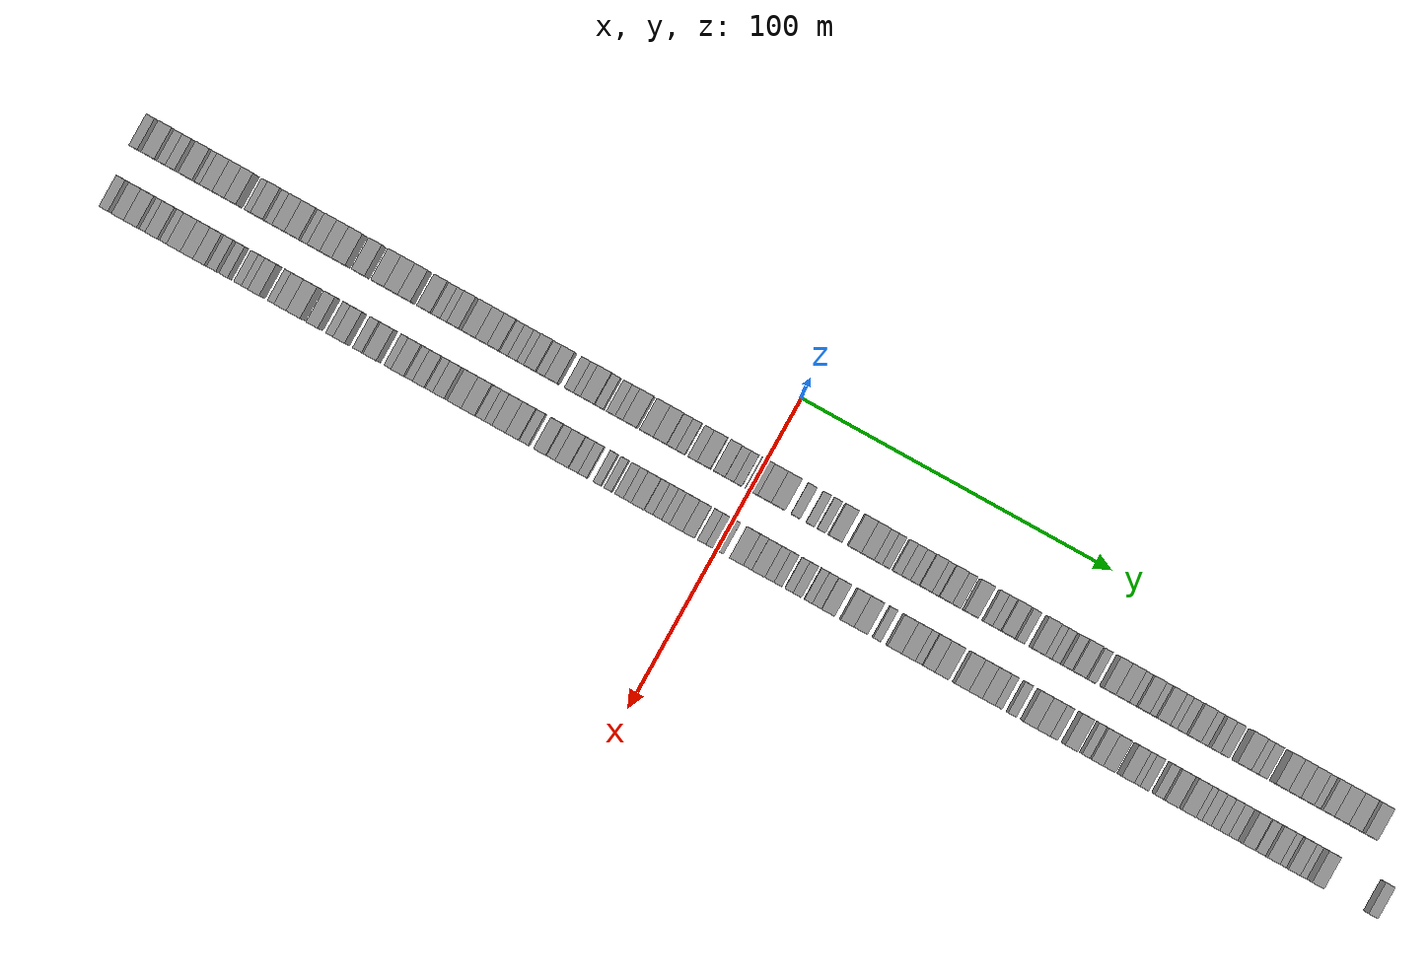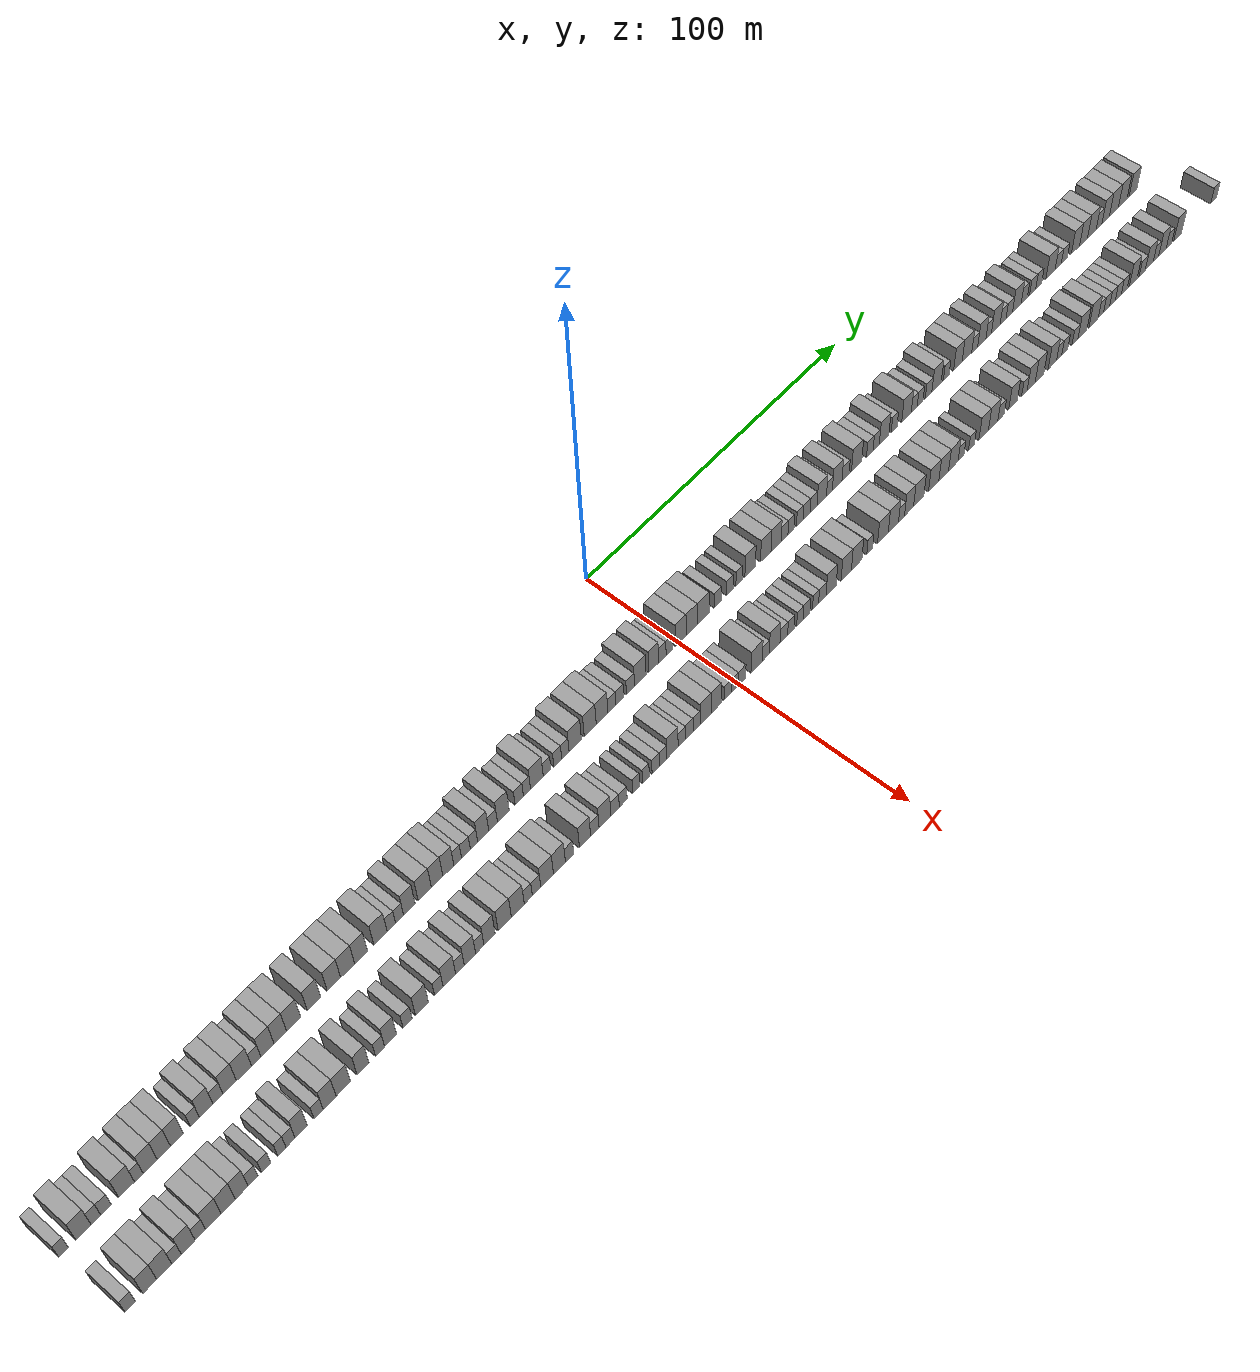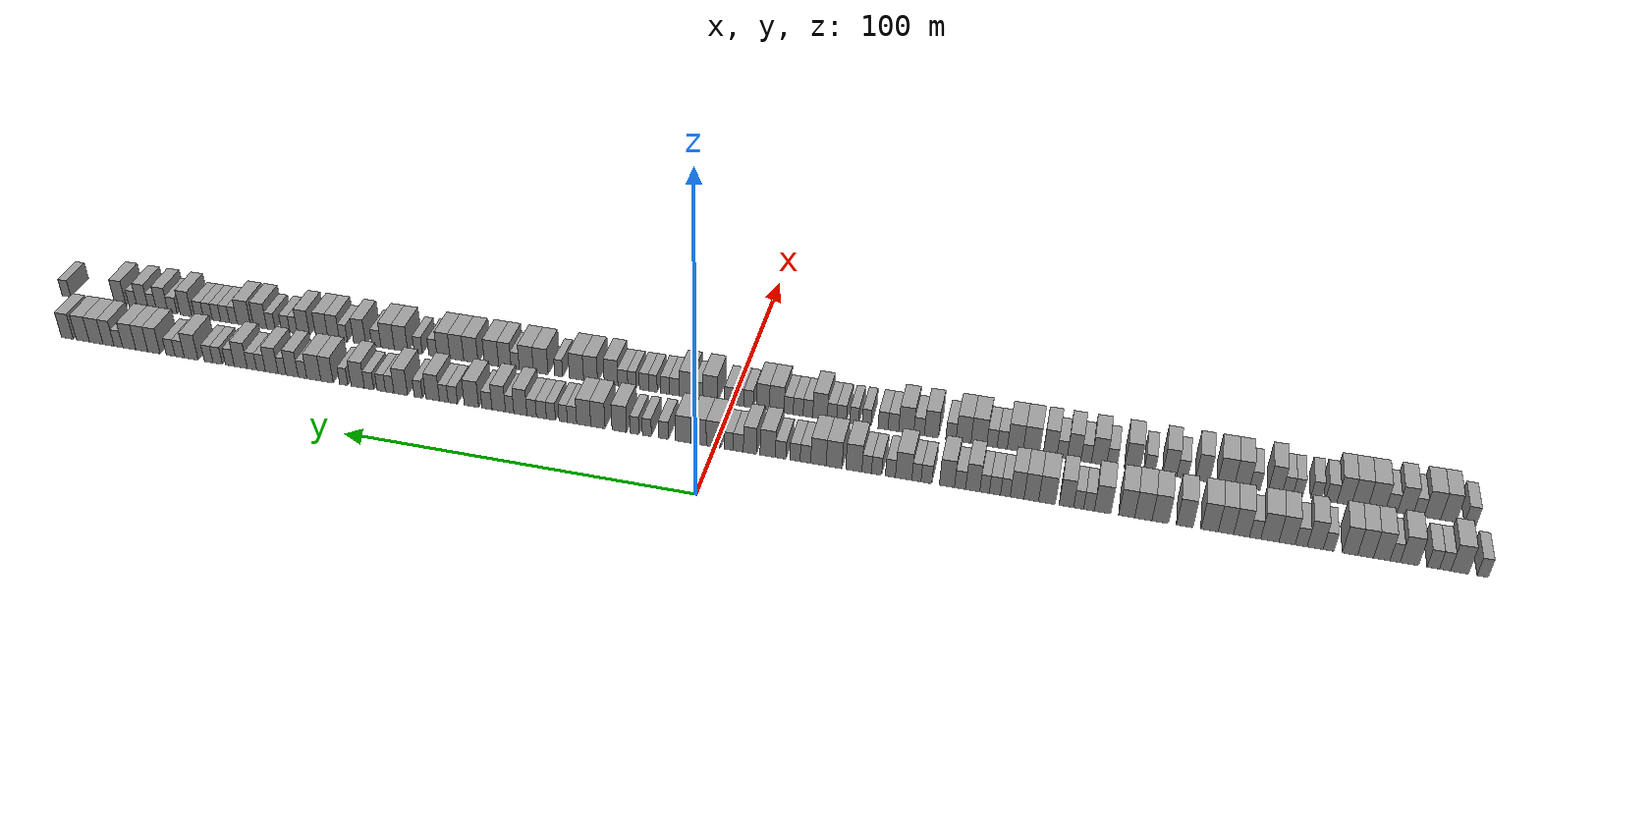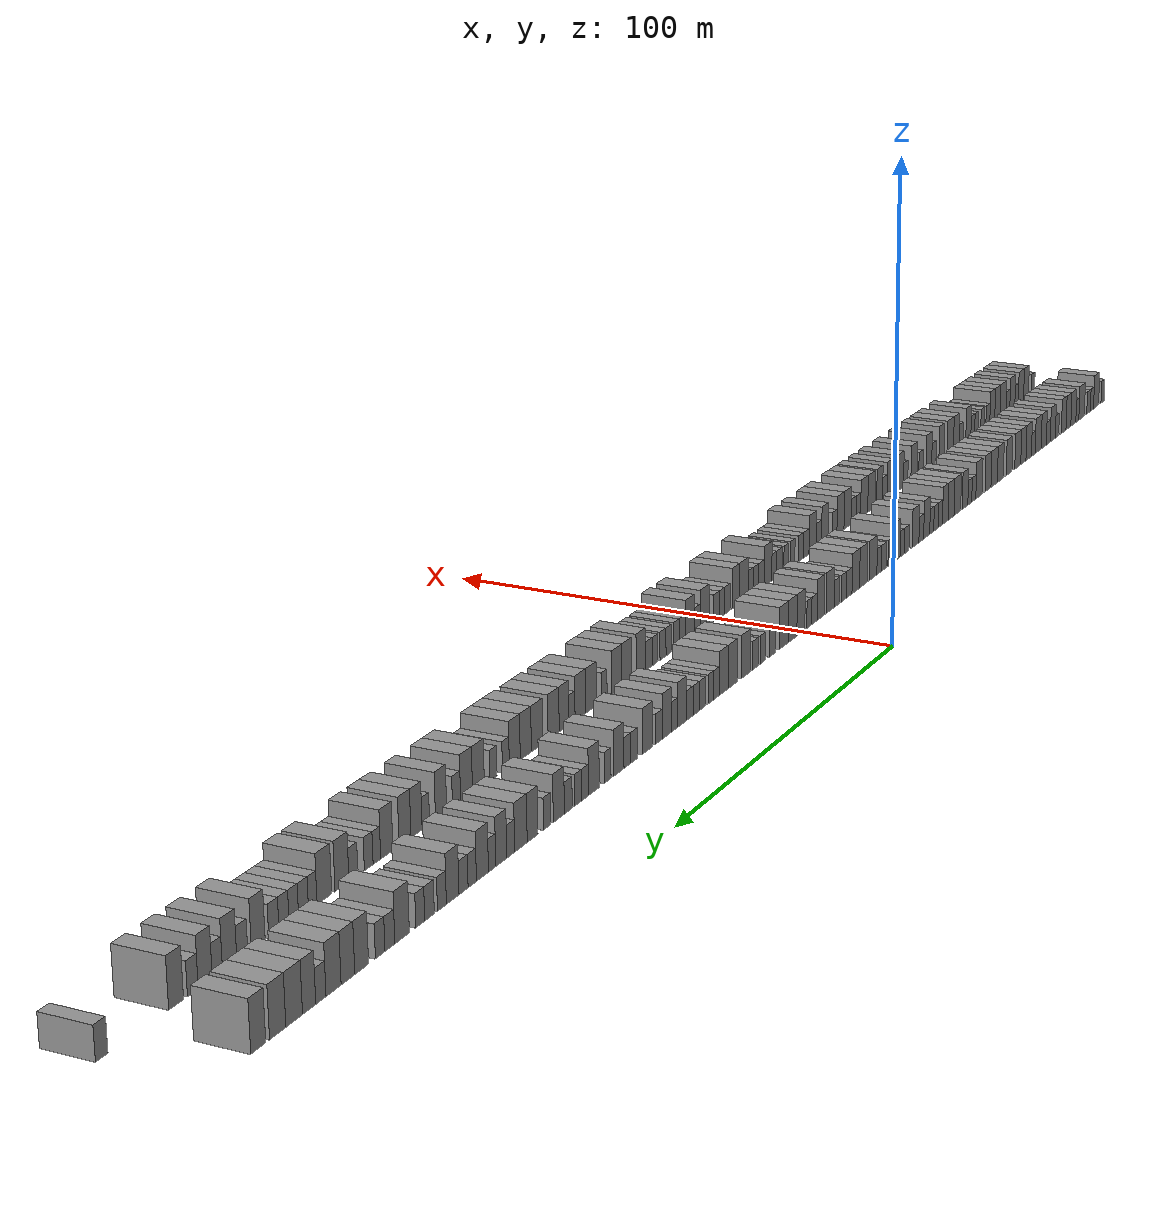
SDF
<sdf version="1.6">
 <world name="default">
  <scene>
   <sky><clouds><speed>12</speed></clouds></sky>
   <ambient>0.4 0.4 0.4 1</ambient>
   <background>0.7 0.7 0.7 1</background>
   <shadows>1</shadows>
  </scene>
  <gravity>0 0 -9.8066</gravity>
  <magnetic_field>6e-06 2.3e-05 -4.2e-05</magnetic_field>
  <physics default="0" name="default_physics" type="ode">
   <ode>
    <solver>
     <type>quick</type>
     <iters>10</iters>
     <sor>1.0</sor>
     <use_dynamic_moi_rescaling>0</use_dynamic_moi_rescaling>
    </solver>
    <constraints>
     <cfm>0</cfm>
     <erp>0.2</erp>
     <contact_max_correcting_vel>100</contact_max_correcting_vel>
     <contact_surface_layer>0.001</contact_surface_layer>
    </constraints>
   </ode>
   <max_step_size>0.004</max_step_size>
   <real_time_factor>1</real_time_factor>
   <real_time_update_rate>250</real_time_update_rate>
  </physics>
  <light name="sun" type="directional">
   <pose>0 0 10 0 0 0</pose>
   <diffuse>0.8 0.8 0.8 1</diffuse>
   <specular>0.2 0.2 0.2 1</specular>
   <attenuation>
    <range>1000</range>
    <constant>0.9</constant>
    <linear>0.01</linear>
    <quadratic>0.001</quadratic>
   </attenuation>
   <direction>-0.5 0.1 -0.9</direction>
  </light>
  <model name="building_1">
   <static>1</static>
   <pose>25.0000 -196.6738 0 0.000000 0.000000 0.000000</pose>
   <link name="link">
    <pose>0 0 3.00 0 0 0</pose>
    <collision name="collision"><geometry><box><size>10.0000 2.6524 6.0000</size></box></geometry></collision>
    <visual name="visual">
     <cast_shadows>0</cast_shadows>
     <geometry><box><size>10.0000 2.6524 6.0000</size></box></geometry>
     <material>
      <script>
       <uri>model://grey_wall/materials/scripts</uri>
       <uri>model://grey_wall/materials/textures</uri>
       <name>vrc/grey_wall</name>
      </script>
     </material>
    </visual>
   </link>
  </model>
  <model name="building_2">
   <static>1</static>
   <pose>25.0000 -191.2391 0 0.000000 0.000000 0.000000</pose>
   <link name="link">
    <pose>0 0 4.50 0 0 0</pose>
    <collision name="collision"><geometry><box><size>10.0000 4.2170 9.0000</size></box></geometry></collision>
    <visual name="visual">
     <cast_shadows>0</cast_shadows>
     <geometry><box><size>10.0000 4.2170 9.0000</size></box></geometry>
     <material>
      <script>
       <uri>model://grey_wall/materials/scripts</uri>
       <uri>model://grey_wall/materials/textures</uri>
       <name>vrc/grey_wall</name>
      </script>
     </material>
    </visual>
   </link>
  </model>
  <model name="building_3">
   <static>1</static>
   <pose>25.0000 -187.8064 0 0.000000 0.000000 0.000000</pose>
   <link name="link">
    <pose>0 0 3.00 0 0 0</pose>
    <collision name="collision"><geometry><box><size>10.0000 2.6485 6.0000</size></box></geometry></collision>
    <visual name="visual">
     <cast_shadows>0</cast_shadows>
     <geometry><box><size>10.0000 2.6485 6.0000</size></box></geometry>
     <material>
      <script>
       <uri>model://grey_wall/materials/scripts</uri>
       <uri>model://grey_wall/materials/textures</uri>
       <name>vrc/grey_wall</name>
      </script>
     </material>
    </visual>
   </link>
  </model>
  <model name="building_4">
   <static>1</static>
   <pose>25.0000 -185.0159 0 0.000000 0.000000 0.000000</pose>
   <link name="link">
    <pose>0 0 3.00 0 0 0</pose>
    <collision name="collision"><geometry><box><size>10.0000 2.9325 6.0000</size></box></geometry></collision>
    <visual name="visual">
     <cast_shadows>0</cast_shadows>
     <geometry><box><size>10.0000 2.9325 6.0000</size></box></geometry>
     <material>
      <script>
       <uri>model://grey_wall/materials/scripts</uri>
       <uri>model://grey_wall/materials/textures</uri>
       <name>vrc/grey_wall</name>
      </script>
     </material>
    </visual>
   </link>
  </model>
  <model name="building_5">
   <static>1</static>
   <pose>25.0000 -179.3387 0 0.000000 0.000000 0.000000</pose>
   <link name="link">
    <pose>0 0 4.50 0 0 0</pose>
    <collision name="collision"><geometry><box><size>10.0000 4.4220 9.0000</size></box></geometry></collision>
    <visual name="visual">
     <cast_shadows>0</cast_shadows>
     <geometry><box><size>10.0000 4.4220 9.0000</size></box></geometry>
     <material>
      <script>
       <uri>model://grey_wall/materials/scripts</uri>
       <uri>model://grey_wall/materials/textures</uri>
       <name>vrc/grey_wall</name>
      </script>
     </material>
    </visual>
   </link>
  </model>
  <model name="building_6">
   <static>1</static>
   <pose>25.0000 -175.9205 0 0.000000 0.000000 0.000000</pose>
   <link name="link">
    <pose>0 0 3.00 0 0 0</pose>
    <collision name="collision"><geometry><box><size>10.0000 2.4143 6.0000</size></box></geometry></collision>
    <visual name="visual">
     <cast_shadows>0</cast_shadows>
     <geometry><box><size>10.0000 2.4143 6.0000</size></box></geometry>
     <material>
      <script>
       <uri>model://grey_wall/materials/scripts</uri>
       <uri>model://grey_wall/materials/textures</uri>
       <name>vrc/grey_wall</name>
      </script>
     </material>
    </visual>
   </link>
  </model>
  <model name="building_7">
   <static>1</static>
   <pose>25.0000 -172.7269 0 0.000000 0.000000 0.000000</pose>
   <link name="link">
    <pose>0 0 4.50 0 0 0</pose>
    <collision name="collision"><geometry><box><size>10.0000 3.9730 9.0000</size></box></geometry></collision>
    <visual name="visual">
     <cast_shadows>0</cast_shadows>
     <geometry><box><size>10.0000 3.9730 9.0000</size></box></geometry>
     <material>
      <script>
       <uri>model://grey_wall/materials/scripts</uri>
       <uri>model://grey_wall/materials/textures</uri>
       <name>vrc/grey_wall</name>
      </script>
     </material>
    </visual>
   </link>
  </model>
  <model name="building_8">
   <static>1</static>
   <pose>25.0000 -168.8402 0 0.000000 0.000000 0.000000</pose>
   <link name="link">
    <pose>0 0 4.50 0 0 0</pose>
    <collision name="collision"><geometry><box><size>10.0000 3.8005 9.0000</size></box></geometry></collision>
    <visual name="visual">
     <cast_shadows>0</cast_shadows>
     <geometry><box><size>10.0000 3.8005 9.0000</size></box></geometry>
     <material>
      <script>
       <uri>model://grey_wall/materials/scripts</uri>
       <uri>model://grey_wall/materials/textures</uri>
       <name>vrc/grey_wall</name>
      </script>
     </material>
    </visual>
   </link>
  </model>
  <model name="building_9">
   <static>1</static>
   <pose>25.0000 -165.0869 0 0.000000 0.000000 0.000000</pose>
   <link name="link">
    <pose>0 0 4.50 0 0 0</pose>
    <collision name="collision"><geometry><box><size>10.0000 3.7061 9.0000</size></box></geometry></collision>
    <visual name="visual">
     <cast_shadows>0</cast_shadows>
     <geometry><box><size>10.0000 3.7061 9.0000</size></box></geometry>
     <material>
      <script>
       <uri>model://grey_wall/materials/scripts</uri>
       <uri>model://grey_wall/materials/textures</uri>
       <name>vrc/grey_wall</name>
      </script>
     </material>
    </visual>
   </link>
  </model>
  <model name="building_10">
   <static>1</static>
   <pose>25.0000 -159.9245 0 0.000000 0.000000 0.000000</pose>
   <link name="link">
    <pose>0 0 3.00 0 0 0</pose>
    <collision name="collision"><geometry><box><size>10.0000 2.6185 6.0000</size></box></geometry></collision>
    <visual name="visual">
     <cast_shadows>0</cast_shadows>
     <geometry><box><size>10.0000 2.6185 6.0000</size></box></geometry>
     <material>
      <script>
       <uri>model://grey_wall/materials/scripts</uri>
       <uri>model://grey_wall/materials/textures</uri>
       <name>vrc/grey_wall</name>
      </script>
     </material>
    </visual>
   </link>
  </model>
  <model name="building_11">
   <static>1</static>
   <pose>25.0000 -156.6583 0 0.000000 0.000000 0.000000</pose>
   <link name="link">
    <pose>0 0 4.50 0 0 0</pose>
    <collision name="collision"><geometry><box><size>10.0000 3.9140 9.0000</size></box></geometry></collision>
    <visual name="visual">
     <cast_shadows>0</cast_shadows>
     <geometry><box><size>10.0000 3.9140 9.0000</size></box></geometry>
     <material>
      <script>
       <uri>model://grey_wall/materials/scripts</uri>
       <uri>model://grey_wall/materials/textures</uri>
       <name>vrc/grey_wall</name>
      </script>
     </material>
    </visual>
   </link>
  </model>
  <model name="building_12">
   <static>1</static>
   <pose>25.0000 -153.2270 0 0.000000 0.000000 0.000000</pose>
   <link name="link">
    <pose>0 0 3.00 0 0 0</pose>
    <collision name="collision"><geometry><box><size>10.0000 2.9485 6.0000</size></box></geometry></collision>
    <visual name="visual">
     <cast_shadows>0</cast_shadows>
     <geometry><box><size>10.0000 2.9485 6.0000</size></box></geometry>
     <material>
      <script>
       <uri>model://grey_wall/materials/scripts</uri>
       <uri>model://grey_wall/materials/textures</uri>
       <name>vrc/grey_wall</name>
      </script>
     </material>
    </visual>
   </link>
  </model>
  <model name="building_13">
   <static>1</static>
   <pose>25.0000 -149.7778 0 0.000000 0.000000 0.000000</pose>
   <link name="link">
    <pose>0 0 4.50 0 0 0</pose>
    <collision name="collision"><geometry><box><size>10.0000 3.9499 9.0000</size></box></geometry></collision>
    <visual name="visual">
     <cast_shadows>0</cast_shadows>
     <geometry><box><size>10.0000 3.9499 9.0000</size></box></geometry>
     <material>
      <script>
       <uri>model://grey_wall/materials/scripts</uri>
       <uri>model://grey_wall/materials/textures</uri>
       <name>vrc/grey_wall</name>
      </script>
     </material>
    </visual>
   </link>
  </model>
  <model name="building_14">
   <static>1</static>
   <pose>25.0000 -145.5605 0 0.000000 0.000000 0.000000</pose>
   <link name="link">
    <pose>0 0 4.50 0 0 0</pose>
    <collision name="collision"><geometry><box><size>10.0000 4.4847 9.0000</size></box></geometry></collision>
    <visual name="visual">
     <cast_shadows>0</cast_shadows>
     <geometry><box><size>10.0000 4.4847 9.0000</size></box></geometry>
     <material>
      <script>
       <uri>model://grey_wall/materials/scripts</uri>
       <uri>model://grey_wall/materials/textures</uri>
       <name>vrc/grey_wall</name>
      </script>
     </material>
    </visual>
   </link>
  </model>
  <model name="building_15">
   <static>1</static>
   <pose>25.0000 -141.9328 0 0.000000 0.000000 0.000000</pose>
   <link name="link">
    <pose>0 0 3.00 0 0 0</pose>
    <collision name="collision"><geometry><box><size>10.0000 2.7708 6.0000</size></box></geometry></collision>
    <visual name="visual">
     <cast_shadows>0</cast_shadows>
     <geometry><box><size>10.0000 2.7708 6.0000</size></box></geometry>
     <material>
      <script>
       <uri>model://grey_wall/materials/scripts</uri>
       <uri>model://grey_wall/materials/textures</uri>
       <name>vrc/grey_wall</name>
      </script>
     </material>
    </visual>
   </link>
  </model>
  <model name="building_16">
   <static>1</static>
   <pose>25.0000 -138.5740 0 0.000000 0.000000 0.000000</pose>
   <link name="link">
    <pose>0 0 4.50 0 0 0</pose>
    <collision name="collision"><geometry><box><size>10.0000 3.9467 9.0000</size></box></geometry></collision>
    <visual name="visual">
     <cast_shadows>0</cast_shadows>
     <geometry><box><size>10.0000 3.9467 9.0000</size></box></geometry>
     <material>
      <script>
       <uri>model://grey_wall/materials/scripts</uri>
       <uri>model://grey_wall/materials/textures</uri>
       <name>vrc/grey_wall</name>
      </script>
     </material>
    </visual>
   </link>
  </model>
  <model name="building_17">
   <static>1</static>
   <pose>25.0000 -134.7032 0 0.000000 0.000000 0.000000</pose>
   <link name="link">
    <pose>0 0 4.50 0 0 0</pose>
    <collision name="collision"><geometry><box><size>10.0000 3.7951 9.0000</size></box></geometry></collision>
    <visual name="visual">
     <cast_shadows>0</cast_shadows>
     <geometry><box><size>10.0000 3.7951 9.0000</size></box></geometry>
     <material>
      <script>
       <uri>model://grey_wall/materials/scripts</uri>
       <uri>model://grey_wall/materials/textures</uri>
       <name>vrc/grey_wall</name>
      </script>
     </material>
    </visual>
   </link>
  </model>
  <model name="building_18">
   <static>1</static>
   <pose>25.0000 -130.6497 0 0.000000 0.000000 0.000000</pose>
   <link name="link">
    <pose>0 0 4.50 0 0 0</pose>
    <collision name="collision"><geometry><box><size>10.0000 4.3119 9.0000</size></box></geometry></collision>
    <visual name="visual">
     <cast_shadows>0</cast_shadows>
     <geometry><box><size>10.0000 4.3119 9.0000</size></box></geometry>
     <material>
      <script>
       <uri>model://grey_wall/materials/scripts</uri>
       <uri>model://grey_wall/materials/textures</uri>
       <name>vrc/grey_wall</name>
      </script>
     </material>
    </visual>
   </link>
  </model>
  <model name="building_19">
   <static>1</static>
   <pose>25.0000 -124.4272 0 0.000000 0.000000 0.000000</pose>
   <link name="link">
    <pose>0 0 4.50 0 0 0</pose>
    <collision name="collision"><geometry><box><size>10.0000 4.1331 9.0000</size></box></geometry></collision>
    <visual name="visual">
     <cast_shadows>0</cast_shadows>
     <geometry><box><size>10.0000 4.1331 9.0000</size></box></geometry>
     <material>
      <script>
       <uri>model://grey_wall/materials/scripts</uri>
       <uri>model://grey_wall/materials/textures</uri>
       <name>vrc/grey_wall</name>
      </script>
     </material>
    </visual>
   </link>
  </model>
  <model name="building_20">
   <static>1</static>
   <pose>25.0000 -118.2726 0 0.000000 0.000000 0.000000</pose>
   <link name="link">
    <pose>0 0 4.50 0 0 0</pose>
    <collision name="collision"><geometry><box><size>10.0000 4.1760 9.0000</size></box></geometry></collision>
    <visual name="visual">
     <cast_shadows>0</cast_shadows>
     <geometry><box><size>10.0000 4.1760 9.0000</size></box></geometry>
     <material>
      <script>
       <uri>model://grey_wall/materials/scripts</uri>
       <uri>model://grey_wall/materials/textures</uri>
       <name>vrc/grey_wall</name>
      </script>
     </material>
    </visual>
   </link>
  </model>
  <model name="building_21">
   <static>1</static>
   <pose>25.0000 -113.9868 0 0.000000 0.000000 0.000000</pose>
   <link name="link">
    <pose>0 0 4.50 0 0 0</pose>
    <collision name="collision"><geometry><box><size>10.0000 4.3957 9.0000</size></box></geometry></collision>
    <visual name="visual">
     <cast_shadows>0</cast_shadows>
     <geometry><box><size>10.0000 4.3957 9.0000</size></box></geometry>
     <material>
      <script>
       <uri>model://grey_wall/materials/scripts</uri>
       <uri>model://grey_wall/materials/textures</uri>
       <name>vrc/grey_wall</name>
      </script>
     </material>
    </visual>
   </link>
  </model>
  <model name="building_22">
   <static>1</static>
   <pose>25.0000 -109.7643 0 0.000000 0.000000 0.000000</pose>
   <link name="link">
    <pose>0 0 4.50 0 0 0</pose>
    <collision name="collision"><geometry><box><size>10.0000 4.0492 9.0000</size></box></geometry></collision>
    <visual name="visual">
     <cast_shadows>0</cast_shadows>
     <geometry><box><size>10.0000 4.0492 9.0000</size></box></geometry>
     <material>
      <script>
       <uri>model://grey_wall/materials/scripts</uri>
       <uri>model://grey_wall/materials/textures</uri>
       <name>vrc/grey_wall</name>
      </script>
     </material>
    </visual>
   </link>
  </model>
  <model name="building_23">
   <static>1</static>
   <pose>25.0000 -103.6163 0 0.000000 0.000000 0.000000</pose>
   <link name="link">
    <pose>0 0 4.50 0 0 0</pose>
    <collision name="collision"><geometry><box><size>10.0000 4.2467 9.0000</size></box></geometry></collision>
    <visual name="visual">
     <cast_shadows>0</cast_shadows>
     <geometry><box><size>10.0000 4.2467 9.0000</size></box></geometry>
     <material>
      <script>
       <uri>model://grey_wall/materials/scripts</uri>
       <uri>model://grey_wall/materials/textures</uri>
       <name>vrc/grey_wall</name>
      </script>
     </material>
    </visual>
   </link>
  </model>
  <model name="building_24">
   <static>1</static>
   <pose>25.0000 -100.1318 0 0.000000 0.000000 0.000000</pose>
   <link name="link">
    <pose>0 0 3.00 0 0 0</pose>
    <collision name="collision"><geometry><box><size>10.0000 2.7223 6.0000</size></box></geometry></collision>
    <visual name="visual">
     <cast_shadows>0</cast_shadows>
     <geometry><box><size>10.0000 2.7223 6.0000</size></box></geometry>
     <material>
      <script>
       <uri>model://grey_wall/materials/scripts</uri>
       <uri>model://grey_wall/materials/textures</uri>
       <name>vrc/grey_wall</name>
      </script>
     </material>
    </visual>
   </link>
  </model>
  <model name="building_25">
   <static>1</static>
   <pose>25.0000 -97.4797 0 0.000000 0.000000 0.000000</pose>
   <link name="link">
    <pose>0 0 3.00 0 0 0</pose>
    <collision name="collision"><geometry><box><size>10.0000 2.5819 6.0000</size></box></geometry></collision>
    <visual name="visual">
     <cast_shadows>0</cast_shadows>
     <geometry><box><size>10.0000 2.5819 6.0000</size></box></geometry>
     <material>
      <script>
       <uri>model://grey_wall/materials/scripts</uri>
       <uri>model://grey_wall/materials/textures</uri>
       <name>vrc/grey_wall</name>
      </script>
     </material>
    </visual>
   </link>
  </model>
  <model name="building_26">
   <static>1</static>
   <pose>25.0000 -94.3275 0 0.000000 0.000000 0.000000</pose>
   <link name="link">
    <pose>0 0 4.50 0 0 0</pose>
    <collision name="collision"><geometry><box><size>10.0000 3.7225 9.0000</size></box></geometry></collision>
    <visual name="visual">
     <cast_shadows>0</cast_shadows>
     <geometry><box><size>10.0000 3.7225 9.0000</size></box></geometry>
     <material>
      <script>
       <uri>model://grey_wall/materials/scripts</uri>
       <uri>model://grey_wall/materials/textures</uri>
       <name>vrc/grey_wall</name>
      </script>
     </material>
    </visual>
   </link>
  </model>
  <model name="building_27">
   <static>1</static>
   <pose>25.0000 -89.3020 0 0.000000 0.000000 0.000000</pose>
   <link name="link">
    <pose>0 0 4.50 0 0 0</pose>
    <collision name="collision"><geometry><box><size>10.0000 4.3286 9.0000</size></box></geometry></collision>
    <visual name="visual">
     <cast_shadows>0</cast_shadows>
     <geometry><box><size>10.0000 4.3286 9.0000</size></box></geometry>
     <material>
      <script>
       <uri>model://grey_wall/materials/scripts</uri>
       <uri>model://grey_wall/materials/textures</uri>
       <name>vrc/grey_wall</name>
      </script>
     </material>
    </visual>
   </link>
  </model>
  <model name="building_28">
   <static>1</static>
   <pose>25.0000 -85.2494 0 0.000000 0.000000 0.000000</pose>
   <link name="link">
    <pose>0 0 4.50 0 0 0</pose>
    <collision name="collision"><geometry><box><size>10.0000 3.7765 9.0000</size></box></geometry></collision>
    <visual name="visual">
     <cast_shadows>0</cast_shadows>
     <geometry><box><size>10.0000 3.7765 9.0000</size></box></geometry>
     <material>
      <script>
       <uri>model://grey_wall/materials/scripts</uri>
       <uri>model://grey_wall/materials/textures</uri>
       <name>vrc/grey_wall</name>
      </script>
     </material>
    </visual>
   </link>
  </model>
  <model name="building_29">
   <static>1</static>
   <pose>25.0000 -81.5595 0 0.000000 0.000000 0.000000</pose>
   <link name="link">
    <pose>0 0 4.50 0 0 0</pose>
    <collision name="collision"><geometry><box><size>10.0000 3.6033 9.0000</size></box></geometry></collision>
    <visual name="visual">
     <cast_shadows>0</cast_shadows>
     <geometry><box><size>10.0000 3.6033 9.0000</size></box></geometry>
     <material>
      <script>
       <uri>model://grey_wall/materials/scripts</uri>
       <uri>model://grey_wall/materials/textures</uri>
       <name>vrc/grey_wall</name>
      </script>
     </material>
    </visual>
   </link>
  </model>
  <model name="building_30">
   <static>1</static>
   <pose>25.0000 -78.4887 0 0.000000 0.000000 0.000000</pose>
   <link name="link">
    <pose>0 0 3.00 0 0 0</pose>
    <collision name="collision"><geometry><box><size>10.0000 2.5384 6.0000</size></box></geometry></collision>
    <visual name="visual">
     <cast_shadows>0</cast_shadows>
     <geometry><box><size>10.0000 2.5384 6.0000</size></box></geometry>
     <material>
      <script>
       <uri>model://grey_wall/materials/scripts</uri>
       <uri>model://grey_wall/materials/textures</uri>
       <name>vrc/grey_wall</name>
      </script>
     </material>
    </visual>
   </link>
  </model>
  <model name="building_31">
   <static>1</static>
   <pose>25.0000 -75.7399 0 0.000000 0.000000 0.000000</pose>
   <link name="link">
    <pose>0 0 3.00 0 0 0</pose>
    <collision name="collision"><geometry><box><size>10.0000 2.9591 6.0000</size></box></geometry></collision>
    <visual name="visual">
     <cast_shadows>0</cast_shadows>
     <geometry><box><size>10.0000 2.9591 6.0000</size></box></geometry>
     <material>
      <script>
       <uri>model://grey_wall/materials/scripts</uri>
       <uri>model://grey_wall/materials/textures</uri>
       <name>vrc/grey_wall</name>
      </script>
     </material>
    </visual>
   </link>
  </model>
  <model name="building_32">
   <static>1</static>
   <pose>25.0000 -73.0192 0 0.000000 0.000000 0.000000</pose>
   <link name="link">
    <pose>0 0 3.00 0 0 0</pose>
    <collision name="collision"><geometry><box><size>10.0000 2.4824 6.0000</size></box></geometry></collision>
    <visual name="visual">
     <cast_shadows>0</cast_shadows>
     <geometry><box><size>10.0000 2.4824 6.0000</size></box></geometry>
     <material>
      <script>
       <uri>model://grey_wall/materials/scripts</uri>
       <uri>model://grey_wall/materials/textures</uri>
       <name>vrc/grey_wall</name>
      </script>
     </material>
    </visual>
   </link>
  </model>
  <model name="building_33">
   <static>1</static>
   <pose>25.0000 -69.9044 0 0.000000 0.000000 0.000000</pose>
   <link name="link">
    <pose>0 0 4.50 0 0 0</pose>
    <collision name="collision"><geometry><box><size>10.0000 3.7471 9.0000</size></box></geometry></collision>
    <visual name="visual">
     <cast_shadows>0</cast_shadows>
     <geometry><box><size>10.0000 3.7471 9.0000</size></box></geometry>
     <material>
      <script>
       <uri>model://grey_wall/materials/scripts</uri>
       <uri>model://grey_wall/materials/textures</uri>
       <name>vrc/grey_wall</name>
      </script>
     </material>
    </visual>
   </link>
  </model>
  <model name="building_34">
   <static>1</static>
   <pose>25.0000 -66.5628 0 0.000000 0.000000 0.000000</pose>
   <link name="link">
    <pose>0 0 3.00 0 0 0</pose>
    <collision name="collision"><geometry><box><size>10.0000 2.9362 6.0000</size></box></geometry></collision>
    <visual name="visual">
     <cast_shadows>0</cast_shadows>
     <geometry><box><size>10.0000 2.9362 6.0000</size></box></geometry>
     <material>
      <script>
       <uri>model://grey_wall/materials/scripts</uri>
       <uri>model://grey_wall/materials/textures</uri>
       <name>vrc/grey_wall</name>
      </script>
     </material>
    </visual>
   </link>
  </model>
  <model name="building_35">
   <static>1</static>
   <pose>25.0000 -63.0881 0 0.000000 0.000000 0.000000</pose>
   <link name="link">
    <pose>0 0 4.50 0 0 0</pose>
    <collision name="collision"><geometry><box><size>10.0000 4.0131 9.0000</size></box></geometry></collision>
    <visual name="visual">
     <cast_shadows>0</cast_shadows>
     <geometry><box><size>10.0000 4.0131 9.0000</size></box></geometry>
     <material>
      <script>
       <uri>model://grey_wall/materials/scripts</uri>
       <uri>model://grey_wall/materials/textures</uri>
       <name>vrc/grey_wall</name>
      </script>
     </material>
    </visual>
   </link>
  </model>
  <model name="building_36">
   <static>1</static>
   <pose>25.0000 -57.6339 0 0.000000 0.000000 0.000000</pose>
   <link name="link">
    <pose>0 0 3.00 0 0 0</pose>
    <collision name="collision"><geometry><box><size>10.0000 2.8952 6.0000</size></box></geometry></collision>
    <visual name="visual">
     <cast_shadows>0</cast_shadows>
     <geometry><box><size>10.0000 2.8952 6.0000</size></box></geometry>
     <material>
      <script>
       <uri>model://grey_wall/materials/scripts</uri>
       <uri>model://grey_wall/materials/textures</uri>
       <name>vrc/grey_wall</name>
      </script>
     </material>
    </visual>
   </link>
  </model>
  <model name="building_37">
   <static>1</static>
   <pose>25.0000 -54.9619 0 0.000000 0.000000 0.000000</pose>
   <link name="link">
    <pose>0 0 3.00 0 0 0</pose>
    <collision name="collision"><geometry><box><size>10.0000 2.4487 6.0000</size></box></geometry></collision>
    <visual name="visual">
     <cast_shadows>0</cast_shadows>
     <geometry><box><size>10.0000 2.4487 6.0000</size></box></geometry>
     <material>
      <script>
       <uri>model://grey_wall/materials/scripts</uri>
       <uri>model://grey_wall/materials/textures</uri>
       <name>vrc/grey_wall</name>
      </script>
     </material>
    </visual>
   </link>
  </model>
  <model name="building_38">
   <static>1</static>
   <pose>25.0000 -51.5327 0 0.000000 0.000000 0.000000</pose>
   <link name="link">
    <pose>0 0 4.50 0 0 0</pose>
    <collision name="collision"><geometry><box><size>10.0000 4.4098 9.0000</size></box></geometry></collision>
    <visual name="visual">
     <cast_shadows>0</cast_shadows>
     <geometry><box><size>10.0000 4.4098 9.0000</size></box></geometry>
     <material>
      <script>
       <uri>model://grey_wall/materials/scripts</uri>
       <uri>model://grey_wall/materials/textures</uri>
       <name>vrc/grey_wall</name>
      </script>
     </material>
    </visual>
   </link>
  </model>
  <model name="building_39">
   <static>1</static>
   <pose>25.0000 -47.9887 0 0.000000 0.000000 0.000000</pose>
   <link name="link">
    <pose>0 0 3.00 0 0 0</pose>
    <collision name="collision"><geometry><box><size>10.0000 2.6781 6.0000</size></box></geometry></collision>
    <visual name="visual">
     <cast_shadows>0</cast_shadows>
     <geometry><box><size>10.0000 2.6781 6.0000</size></box></geometry>
     <material>
      <script>
       <uri>model://grey_wall/materials/scripts</uri>
       <uri>model://grey_wall/materials/textures</uri>
       <name>vrc/grey_wall</name>
      </script>
     </material>
    </visual>
   </link>
  </model>
  <model name="building_40">
   <static>1</static>
   <pose>25.0000 -44.2645 0 0.000000 0.000000 0.000000</pose>
   <link name="link">
    <pose>0 0 3.00 0 0 0</pose>
    <collision name="collision"><geometry><box><size>10.0000 2.7703 6.0000</size></box></geometry></collision>
    <visual name="visual">
     <cast_shadows>0</cast_shadows>
     <geometry><box><size>10.0000 2.7703 6.0000</size></box></geometry>
     <material>
      <script>
       <uri>model://grey_wall/materials/scripts</uri>
       <uri>model://grey_wall/materials/textures</uri>
       <name>vrc/grey_wall</name>
      </script>
     </material>
    </visual>
   </link>
  </model>
  <model name="building_41">
   <static>1</static>
   <pose>25.0000 -41.5869 0 0.000000 0.000000 0.000000</pose>
   <link name="link">
    <pose>0 0 3.00 0 0 0</pose>
    <collision name="collision"><geometry><box><size>10.0000 2.5850 6.0000</size></box></geometry></collision>
    <visual name="visual">
     <cast_shadows>0</cast_shadows>
     <geometry><box><size>10.0000 2.5850 6.0000</size></box></geometry>
     <material>
      <script>
       <uri>model://grey_wall/materials/scripts</uri>
       <uri>model://grey_wall/materials/textures</uri>
       <name>vrc/grey_wall</name>
      </script>
     </material>
    </visual>
   </link>
  </model>
  <model name="building_42">
   <static>1</static>
   <pose>25.0000 -38.0971 0 0.000000 0.000000 0.000000</pose>
   <link name="link">
    <pose>0 0 4.50 0 0 0</pose>
    <collision name="collision"><geometry><box><size>10.0000 4.3944 9.0000</size></box></geometry></collision>
    <visual name="visual">
     <cast_shadows>0</cast_shadows>
     <geometry><box><size>10.0000 4.3944 9.0000</size></box></geometry>
     <material>
      <script>
       <uri>model://grey_wall/materials/scripts</uri>
       <uri>model://grey_wall/materials/textures</uri>
       <name>vrc/grey_wall</name>
      </script>
     </material>
    </visual>
   </link>
  </model>
  <model name="building_43">
   <static>1</static>
   <pose>25.0000 -32.7384 0 0.000000 0.000000 0.000000</pose>
   <link name="link">
    <pose>0 0 4.50 0 0 0</pose>
    <collision name="collision"><geometry><box><size>10.0000 4.3231 9.0000</size></box></geometry></collision>
    <visual name="visual">
     <cast_shadows>0</cast_shadows>
     <geometry><box><size>10.0000 4.3231 9.0000</size></box></geometry>
     <material>
      <script>
       <uri>model://grey_wall/materials/scripts</uri>
       <uri>model://grey_wall/materials/textures</uri>
       <name>vrc/grey_wall</name>
      </script>
     </material>
    </visual>
   </link>
  </model>
  <model name="building_44">
   <static>1</static>
   <pose>25.0000 -28.4641 0 0.000000 0.000000 0.000000</pose>
   <link name="link">
    <pose>0 0 4.50 0 0 0</pose>
    <collision name="collision"><geometry><box><size>10.0000 4.2255 9.0000</size></box></geometry></collision>
    <visual name="visual">
     <cast_shadows>0</cast_shadows>
     <geometry><box><size>10.0000 4.2255 9.0000</size></box></geometry>
     <material>
      <script>
       <uri>model://grey_wall/materials/scripts</uri>
       <uri>model://grey_wall/materials/textures</uri>
       <name>vrc/grey_wall</name>
      </script>
     </material>
    </visual>
   </link>
  </model>
  <model name="building_45">
   <static>1</static>
   <pose>25.0000 -24.9012 0 0.000000 0.000000 0.000000</pose>
   <link name="link">
    <pose>0 0 3.00 0 0 0</pose>
    <collision name="collision"><geometry><box><size>10.0000 2.9003 6.0000</size></box></geometry></collision>
    <visual name="visual">
     <cast_shadows>0</cast_shadows>
     <geometry><box><size>10.0000 2.9003 6.0000</size></box></geometry>
     <material>
      <script>
       <uri>model://grey_wall/materials/scripts</uri>
       <uri>model://grey_wall/materials/textures</uri>
       <name>vrc/grey_wall</name>
      </script>
     </material>
    </visual>
   </link>
  </model>
  <model name="building_46">
   <static>1</static>
   <pose>25.0000 -22.0309 0 0.000000 0.000000 0.000000</pose>
   <link name="link">
    <pose>0 0 3.00 0 0 0</pose>
    <collision name="collision"><geometry><box><size>10.0000 2.8403 6.0000</size></box></geometry></collision>
    <visual name="visual">
     <cast_shadows>0</cast_shadows>
     <geometry><box><size>10.0000 2.8403 6.0000</size></box></geometry>
     <material>
      <script>
       <uri>model://grey_wall/materials/scripts</uri>
       <uri>model://grey_wall/materials/textures</uri>
       <name>vrc/grey_wall</name>
      </script>
     </material>
    </visual>
   </link>
  </model>
  <model name="building_47">
   <static>1</static>
   <pose>25.0000 -18.1240 0 0.000000 0.000000 0.000000</pose>
   <link name="link">
    <pose>0 0 3.00 0 0 0</pose>
    <collision name="collision"><geometry><box><size>10.0000 2.9736 6.0000</size></box></geometry></collision>
    <visual name="visual">
     <cast_shadows>0</cast_shadows>
     <geometry><box><size>10.0000 2.9736 6.0000</size></box></geometry>
     <material>
      <script>
       <uri>model://grey_wall/materials/scripts</uri>
       <uri>model://grey_wall/materials/textures</uri>
       <name>vrc/grey_wall</name>
      </script>
     </material>
    </visual>
   </link>
  </model>
  <model name="building_48">
   <static>1</static>
   <pose>25.0000 -14.5111 0 0.000000 0.000000 0.000000</pose>
   <link name="link">
    <pose>0 0 4.50 0 0 0</pose>
    <collision name="collision"><geometry><box><size>10.0000 4.2522 9.0000</size></box></geometry></collision>
    <visual name="visual">
     <cast_shadows>0</cast_shadows>
     <geometry><box><size>10.0000 4.2522 9.0000</size></box></geometry>
     <material>
      <script>
       <uri>model://grey_wall/materials/scripts</uri>
       <uri>model://grey_wall/materials/textures</uri>
       <name>vrc/grey_wall</name>
      </script>
     </material>
    </visual>
   </link>
  </model>
  <model name="building_49">
   <static>1</static>
   <pose>25.0000 -9.5667 0 0.000000 0.000000 0.000000</pose>
   <link name="link">
    <pose>0 0 4.50 0 0 0</pose>
    <collision name="collision"><geometry><box><size>10.0000 3.6364 9.0000</size></box></geometry></collision>
    <visual name="visual">
     <cast_shadows>0</cast_shadows>
     <geometry><box><size>10.0000 3.6364 9.0000</size></box></geometry>
     <material>
      <script>
       <uri>model://grey_wall/materials/scripts</uri>
       <uri>model://grey_wall/materials/textures</uri>
       <name>vrc/grey_wall</name>
      </script>
     </material>
    </visual>
   </link>
  </model>
  <model name="building_50">
   <static>1</static>
   <pose>25.0000 -6.3420 0 0.000000 0.000000 0.000000</pose>
   <link name="link">
    <pose>0 0 3.00 0 0 0</pose>
    <collision name="collision"><geometry><box><size>10.0000 2.8131 6.0000</size></box></geometry></collision>
    <visual name="visual">
     <cast_shadows>0</cast_shadows>
     <geometry><box><size>10.0000 2.8131 6.0000</size></box></geometry>
     <material>
      <script>
       <uri>model://grey_wall/materials/scripts</uri>
       <uri>model://grey_wall/materials/textures</uri>
       <name>vrc/grey_wall</name>
      </script>
     </material>
    </visual>
   </link>
  </model>
  <model name="building_51">
   <static>1</static>
   <pose>25.0000 -3.6616 0 0.000000 0.000000 0.000000</pose>
   <link name="link">
    <pose>0 0 3.00 0 0 0</pose>
    <collision name="collision"><geometry><box><size>10.0000 2.5476 6.0000</size></box></geometry></collision>
    <visual name="visual">
     <cast_shadows>0</cast_shadows>
     <geometry><box><size>10.0000 2.5476 6.0000</size></box></geometry>
     <material>
      <script>
       <uri>model://grey_wall/materials/scripts</uri>
       <uri>model://grey_wall/materials/textures</uri>
       <name>vrc/grey_wall</name>
      </script>
     </material>
    </visual>
   </link>
  </model>
  <model name="building_52">
   <static>1</static>
   <pose>25.0000 0.6370 0 0.000000 0.000000 0.000000</pose>
   <link name="link">
    <pose>0 0 4.50 0 0 0</pose>
    <collision name="collision"><geometry><box><size>10.0000 4.0496 9.0000</size></box></geometry></collision>
    <visual name="visual">
     <cast_shadows>0</cast_shadows>
     <geometry><box><size>10.0000 4.0496 9.0000</size></box></geometry>
     <material>
      <script>
       <uri>model://grey_wall/materials/scripts</uri>
       <uri>model://grey_wall/materials/textures</uri>
       <name>vrc/grey_wall</name>
      </script>
     </material>
    </visual>
   </link>
  </model>
  <model name="building_53">
   <static>1</static>
   <pose>25.0000 4.7994 0 0.000000 0.000000 0.000000</pose>
   <link name="link">
    <pose>0 0 4.50 0 0 0</pose>
    <collision name="collision"><geometry><box><size>10.0000 4.2754 9.0000</size></box></geometry></collision>
    <visual name="visual">
     <cast_shadows>0</cast_shadows>
     <geometry><box><size>10.0000 4.2754 9.0000</size></box></geometry>
     <material>
      <script>
       <uri>model://grey_wall/materials/scripts</uri>
       <uri>model://grey_wall/materials/textures</uri>
       <name>vrc/grey_wall</name>
      </script>
     </material>
    </visual>
   </link>
  </model>
  <model name="building_54">
   <static>1</static>
   <pose>25.0000 9.1349 0 0.000000 0.000000 0.000000</pose>
   <link name="link">
    <pose>0 0 4.50 0 0 0</pose>
    <collision name="collision"><geometry><box><size>10.0000 4.3956 9.0000</size></box></geometry></collision>
    <visual name="visual">
     <cast_shadows>0</cast_shadows>
     <geometry><box><size>10.0000 4.3956 9.0000</size></box></geometry>
     <material>
      <script>
       <uri>model://grey_wall/materials/scripts</uri>
       <uri>model://grey_wall/materials/textures</uri>
       <name>vrc/grey_wall</name>
      </script>
     </material>
    </visual>
   </link>
  </model>
  <model name="building_55">
   <static>1</static>
   <pose>25.0000 14.7511 0 0.000000 0.000000 0.000000</pose>
   <link name="link">
    <pose>0 0 3.00 0 0 0</pose>
    <collision name="collision"><geometry><box><size>10.0000 2.8367 6.0000</size></box></geometry></collision>
    <visual name="visual">
     <cast_shadows>0</cast_shadows>
     <geometry><box><size>10.0000 2.8367 6.0000</size></box></geometry>
     <material>
      <script>
       <uri>model://grey_wall/materials/scripts</uri>
       <uri>model://grey_wall/materials/textures</uri>
       <name>vrc/grey_wall</name>
      </script>
     </material>
    </visual>
   </link>
  </model>
  <model name="building_56">
   <static>1</static>
   <pose>25.0000 19.4567 0 0.000000 0.000000 0.000000</pose>
   <link name="link">
    <pose>0 0 3.00 0 0 0</pose>
    <collision name="collision"><geometry><box><size>10.0000 2.5744 6.0000</size></box></geometry></collision>
    <visual name="visual">
     <cast_shadows>0</cast_shadows>
     <geometry><box><size>10.0000 2.5744 6.0000</size></box></geometry>
     <material>
      <script>
       <uri>model://grey_wall/materials/scripts</uri>
       <uri>model://grey_wall/materials/textures</uri>
       <name>vrc/grey_wall</name>
      </script>
     </material>
    </visual>
   </link>
  </model>
  <model name="building_57">
   <static>1</static>
   <pose>25.0000 23.0053 0 0.000000 0.000000 0.000000</pose>
   <link name="link">
    <pose>0 0 3.00 0 0 0</pose>
    <collision name="collision"><geometry><box><size>10.0000 2.5229 6.0000</size></box></geometry></collision>
    <visual name="visual">
     <cast_shadows>0</cast_shadows>
     <geometry><box><size>10.0000 2.5229 6.0000</size></box></geometry>
     <material>
      <script>
       <uri>model://grey_wall/materials/scripts</uri>
       <uri>model://grey_wall/materials/textures</uri>
       <name>vrc/grey_wall</name>
      </script>
     </material>
    </visual>
   </link>
  </model>
  <model name="building_58">
   <static>1</static>
   <pose>25.0000 27.3619 0 0.000000 0.000000 0.000000</pose>
   <link name="link">
    <pose>0 0 4.50 0 0 0</pose>
    <collision name="collision"><geometry><box><size>10.0000 4.1903 9.0000</size></box></geometry></collision>
    <visual name="visual">
     <cast_shadows>0</cast_shadows>
     <geometry><box><size>10.0000 4.1903 9.0000</size></box></geometry>
     <material>
      <script>
       <uri>model://grey_wall/materials/scripts</uri>
       <uri>model://grey_wall/materials/textures</uri>
       <name>vrc/grey_wall</name>
      </script>
     </material>
    </visual>
   </link>
  </model>
  <model name="building_59">
   <static>1</static>
   <pose>25.0000 33.5220 0 0.000000 0.000000 0.000000</pose>
   <link name="link">
    <pose>0 0 4.50 0 0 0</pose>
    <collision name="collision"><geometry><box><size>10.0000 4.1299 9.0000</size></box></geometry></collision>
    <visual name="visual">
     <cast_shadows>0</cast_shadows>
     <geometry><box><size>10.0000 4.1299 9.0000</size></box></geometry>
     <material>
      <script>
       <uri>model://grey_wall/materials/scripts</uri>
       <uri>model://grey_wall/materials/textures</uri>
       <name>vrc/grey_wall</name>
      </script>
     </material>
    </visual>
   </link>
  </model>
  <model name="building_60">
   <static>1</static>
   <pose>25.0000 37.6324 0 0.000000 0.000000 0.000000</pose>
   <link name="link">
    <pose>0 0 4.50 0 0 0</pose>
    <collision name="collision"><geometry><box><size>10.0000 4.0908 9.0000</size></box></geometry></collision>
    <visual name="visual">
     <cast_shadows>0</cast_shadows>
     <geometry><box><size>10.0000 4.0908 9.0000</size></box></geometry>
     <material>
      <script>
       <uri>model://grey_wall/materials/scripts</uri>
       <uri>model://grey_wall/materials/textures</uri>
       <name>vrc/grey_wall</name>
      </script>
     </material>
    </visual>
   </link>
  </model>
  <model name="building_61">
   <static>1</static>
   <pose>25.0000 41.0236 0 0.000000 0.000000 0.000000</pose>
   <link name="link">
    <pose>0 0 3.00 0 0 0</pose>
    <collision name="collision"><geometry><box><size>10.0000 2.6917 6.0000</size></box></geometry></collision>
    <visual name="visual">
     <cast_shadows>0</cast_shadows>
     <geometry><box><size>10.0000 2.6917 6.0000</size></box></geometry>
     <material>
      <script>
       <uri>model://grey_wall/materials/scripts</uri>
       <uri>model://grey_wall/materials/textures</uri>
       <name>vrc/grey_wall</name>
      </script>
     </material>
    </visual>
   </link>
  </model>
  <model name="building_62">
   <static>1</static>
   <pose>25.0000 43.5973 0 0.000000 0.000000 0.000000</pose>
   <link name="link">
    <pose>0 0 3.00 0 0 0</pose>
    <collision name="collision"><geometry><box><size>10.0000 2.4557 6.0000</size></box></geometry></collision>
    <visual name="visual">
     <cast_shadows>0</cast_shadows>
     <geometry><box><size>10.0000 2.4557 6.0000</size></box></geometry>
     <material>
      <script>
       <uri>model://grey_wall/materials/scripts</uri>
       <uri>model://grey_wall/materials/textures</uri>
       <name>vrc/grey_wall</name>
      </script>
     </material>
    </visual>
   </link>
  </model>
  <model name="building_63">
   <static>1</static>
   <pose>25.0000 47.1618 0 0.000000 0.000000 0.000000</pose>
   <link name="link">
    <pose>0 0 3.00 0 0 0</pose>
    <collision name="collision"><geometry><box><size>10.0000 2.6733 6.0000</size></box></geometry></collision>
    <visual name="visual">
     <cast_shadows>0</cast_shadows>
     <geometry><box><size>10.0000 2.6733 6.0000</size></box></geometry>
     <material>
      <script>
       <uri>model://grey_wall/materials/scripts</uri>
       <uri>model://grey_wall/materials/textures</uri>
       <name>vrc/grey_wall</name>
      </script>
     </material>
    </visual>
   </link>
  </model>
  <model name="building_64">
   <static>1</static>
   <pose>25.0000 49.9579 0 0.000000 0.000000 0.000000</pose>
   <link name="link">
    <pose>0 0 3.00 0 0 0</pose>
    <collision name="collision"><geometry><box><size>10.0000 2.9188 6.0000</size></box></geometry></collision>
    <visual name="visual">
     <cast_shadows>0</cast_shadows>
     <geometry><box><size>10.0000 2.9188 6.0000</size></box></geometry>
     <material>
      <script>
       <uri>model://grey_wall/materials/scripts</uri>
       <uri>model://grey_wall/materials/textures</uri>
       <name>vrc/grey_wall</name>
      </script>
     </material>
    </visual>
   </link>
  </model>
  <model name="building_65">
   <static>1</static>
   <pose>25.0000 52.8050 0 0.000000 0.000000 0.000000</pose>
   <link name="link">
    <pose>0 0 3.00 0 0 0</pose>
    <collision name="collision"><geometry><box><size>10.0000 2.7754 6.0000</size></box></geometry></collision>
    <visual name="visual">
     <cast_shadows>0</cast_shadows>
     <geometry><box><size>10.0000 2.7754 6.0000</size></box></geometry>
     <material>
      <script>
       <uri>model://grey_wall/materials/scripts</uri>
       <uri>model://grey_wall/materials/textures</uri>
       <name>vrc/grey_wall</name>
      </script>
     </material>
    </visual>
   </link>
  </model>
  <model name="building_66">
   <static>1</static>
   <pose>25.0000 56.1253 0 0.000000 0.000000 0.000000</pose>
   <link name="link">
    <pose>0 0 4.50 0 0 0</pose>
    <collision name="collision"><geometry><box><size>10.0000 3.8653 9.0000</size></box></geometry></collision>
    <visual name="visual">
     <cast_shadows>0</cast_shadows>
     <geometry><box><size>10.0000 3.8653 9.0000</size></box></geometry>
     <material>
      <script>
       <uri>model://grey_wall/materials/scripts</uri>
       <uri>model://grey_wall/materials/textures</uri>
       <name>vrc/grey_wall</name>
      </script>
     </material>
    </visual>
   </link>
  </model>
  <model name="building_67">
   <static>1</static>
   <pose>25.0000 59.2875 0 0.000000 0.000000 0.000000</pose>
   <link name="link">
    <pose>0 0 3.00 0 0 0</pose>
    <collision name="collision"><geometry><box><size>10.0000 2.4591 6.0000</size></box></geometry></collision>
    <visual name="visual">
     <cast_shadows>0</cast_shadows>
     <geometry><box><size>10.0000 2.4591 6.0000</size></box></geometry>
     <material>
      <script>
       <uri>model://grey_wall/materials/scripts</uri>
       <uri>model://grey_wall/materials/textures</uri>
       <name>vrc/grey_wall</name>
      </script>
     </material>
    </visual>
   </link>
  </model>
  <model name="building_68">
   <static>1</static>
   <pose>25.0000 62.5133 0 0.000000 0.000000 0.000000</pose>
   <link name="link">
    <pose>0 0 4.50 0 0 0</pose>
    <collision name="collision"><geometry><box><size>10.0000 3.9925 9.0000</size></box></geometry></collision>
    <visual name="visual">
     <cast_shadows>0</cast_shadows>
     <geometry><box><size>10.0000 3.9925 9.0000</size></box></geometry>
     <material>
      <script>
       <uri>model://grey_wall/materials/scripts</uri>
       <uri>model://grey_wall/materials/textures</uri>
       <name>vrc/grey_wall</name>
      </script>
     </material>
    </visual>
   </link>
  </model>
  <model name="building_69">
   <static>1</static>
   <pose>25.0000 65.9963 0 0.000000 0.000000 0.000000</pose>
   <link name="link">
    <pose>0 0 3.00 0 0 0</pose>
    <collision name="collision"><geometry><box><size>10.0000 2.9735 6.0000</size></box></geometry></collision>
    <visual name="visual">
     <cast_shadows>0</cast_shadows>
     <geometry><box><size>10.0000 2.9735 6.0000</size></box></geometry>
     <material>
      <script>
       <uri>model://grey_wall/materials/scripts</uri>
       <uri>model://grey_wall/materials/textures</uri>
       <name>vrc/grey_wall</name>
      </script>
     </material>
    </visual>
   </link>
  </model>
  <model name="building_70">
   <static>1</static>
   <pose>25.0000 70.6394 0 0.000000 0.000000 0.000000</pose>
   <link name="link">
    <pose>0 0 4.50 0 0 0</pose>
    <collision name="collision"><geometry><box><size>10.0000 4.3127 9.0000</size></box></geometry></collision>
    <visual name="visual">
     <cast_shadows>0</cast_shadows>
     <geometry><box><size>10.0000 4.3127 9.0000</size></box></geometry>
     <material>
      <script>
       <uri>model://grey_wall/materials/scripts</uri>
       <uri>model://grey_wall/materials/textures</uri>
       <name>vrc/grey_wall</name>
      </script>
     </material>
    </visual>
   </link>
  </model>
  <model name="building_71">
   <static>1</static>
   <pose>25.0000 76.1964 0 0.000000 0.000000 0.000000</pose>
   <link name="link">
    <pose>0 0 3.00 0 0 0</pose>
    <collision name="collision"><geometry><box><size>10.0000 2.8014 6.0000</size></box></geometry></collision>
    <visual name="visual">
     <cast_shadows>0</cast_shadows>
     <geometry><box><size>10.0000 2.8014 6.0000</size></box></geometry>
     <material>
      <script>
       <uri>model://grey_wall/materials/scripts</uri>
       <uri>model://grey_wall/materials/textures</uri>
       <name>vrc/grey_wall</name>
      </script>
     </material>
    </visual>
   </link>
  </model>
  <model name="building_72">
   <static>1</static>
   <pose>25.0000 78.9055 0 0.000000 0.000000 0.000000</pose>
   <link name="link">
    <pose>0 0 3.00 0 0 0</pose>
    <collision name="collision"><geometry><box><size>10.0000 2.6168 6.0000</size></box></geometry></collision>
    <visual name="visual">
     <cast_shadows>0</cast_shadows>
     <geometry><box><size>10.0000 2.6168 6.0000</size></box></geometry>
     <material>
      <script>
       <uri>model://grey_wall/materials/scripts</uri>
       <uri>model://grey_wall/materials/textures</uri>
       <name>vrc/grey_wall</name>
      </script>
     </material>
    </visual>
   </link>
  </model>
  <model name="building_73">
   <static>1</static>
   <pose>25.0000 82.2757 0 0.000000 0.000000 0.000000</pose>
   <link name="link">
    <pose>0 0 4.50 0 0 0</pose>
    <collision name="collision"><geometry><box><size>10.0000 4.1236 9.0000</size></box></geometry></collision>
    <visual name="visual">
     <cast_shadows>0</cast_shadows>
     <geometry><box><size>10.0000 4.1236 9.0000</size></box></geometry>
     <material>
      <script>
       <uri>model://grey_wall/materials/scripts</uri>
       <uri>model://grey_wall/materials/textures</uri>
       <name>vrc/grey_wall</name>
      </script>
     </material>
    </visual>
   </link>
  </model>
  <model name="building_74">
   <static>1</static>
   <pose>25.0000 86.5996 0 0.000000 0.000000 0.000000</pose>
   <link name="link">
    <pose>0 0 3.00 0 0 0</pose>
    <collision name="collision"><geometry><box><size>10.0000 2.5241 6.0000</size></box></geometry></collision>
    <visual name="visual">
     <cast_shadows>0</cast_shadows>
     <geometry><box><size>10.0000 2.5241 6.0000</size></box></geometry>
     <material>
      <script>
       <uri>model://grey_wall/materials/scripts</uri>
       <uri>model://grey_wall/materials/textures</uri>
       <name>vrc/grey_wall</name>
      </script>
     </material>
    </visual>
   </link>
  </model>
  <model name="building_75">
   <static>1</static>
   <pose>25.0000 91.9286 0 0.000000 0.000000 0.000000</pose>
   <link name="link">
    <pose>0 0 4.50 0 0 0</pose>
    <collision name="collision"><geometry><box><size>10.0000 4.1339 9.0000</size></box></geometry></collision>
    <visual name="visual">
     <cast_shadows>0</cast_shadows>
     <geometry><box><size>10.0000 4.1339 9.0000</size></box></geometry>
     <material>
      <script>
       <uri>model://grey_wall/materials/scripts</uri>
       <uri>model://grey_wall/materials/textures</uri>
       <name>vrc/grey_wall</name>
      </script>
     </material>
    </visual>
   </link>
  </model>
  <model name="building_76">
   <static>1</static>
   <pose>25.0000 95.2708 0 0.000000 0.000000 0.000000</pose>
   <link name="link">
    <pose>0 0 3.00 0 0 0</pose>
    <collision name="collision"><geometry><box><size>10.0000 2.5506 6.0000</size></box></geometry></collision>
    <visual name="visual">
     <cast_shadows>0</cast_shadows>
     <geometry><box><size>10.0000 2.5506 6.0000</size></box></geometry>
     <material>
      <script>
       <uri>model://grey_wall/materials/scripts</uri>
       <uri>model://grey_wall/materials/textures</uri>
       <name>vrc/grey_wall</name>
      </script>
     </material>
    </visual>
   </link>
  </model>
  <model name="building_77">
   <static>1</static>
   <pose>25.0000 97.8329 0 0.000000 0.000000 0.000000</pose>
   <link name="link">
    <pose>0 0 3.00 0 0 0</pose>
    <collision name="collision"><geometry><box><size>10.0000 2.5735 6.0000</size></box></geometry></collision>
    <visual name="visual">
     <cast_shadows>0</cast_shadows>
     <geometry><box><size>10.0000 2.5735 6.0000</size></box></geometry>
     <material>
      <script>
       <uri>model://grey_wall/materials/scripts</uri>
       <uri>model://grey_wall/materials/textures</uri>
       <name>vrc/grey_wall</name>
      </script>
     </material>
    </visual>
   </link>
  </model>
  <model name="building_78">
   <static>1</static>
   <pose>25.0000 101.5689 0 0.000000 0.000000 0.000000</pose>
   <link name="link">
    <pose>0 0 3.00 0 0 0</pose>
    <collision name="collision"><geometry><box><size>10.0000 2.8985 6.0000</size></box></geometry></collision>
    <visual name="visual">
     <cast_shadows>0</cast_shadows>
     <geometry><box><size>10.0000 2.8985 6.0000</size></box></geometry>
     <material>
      <script>
       <uri>model://grey_wall/materials/scripts</uri>
       <uri>model://grey_wall/materials/textures</uri>
       <name>vrc/grey_wall</name>
      </script>
     </material>
    </visual>
   </link>
  </model>
  <model name="building_79">
   <static>1</static>
   <pose>25.0000 105.0564 0 0.000000 0.000000 0.000000</pose>
   <link name="link">
    <pose>0 0 4.50 0 0 0</pose>
    <collision name="collision"><geometry><box><size>10.0000 4.0766 9.0000</size></box></geometry></collision>
    <visual name="visual">
     <cast_shadows>0</cast_shadows>
     <geometry><box><size>10.0000 4.0766 9.0000</size></box></geometry>
     <material>
      <script>
       <uri>model://grey_wall/materials/scripts</uri>
       <uri>model://grey_wall/materials/textures</uri>
       <name>vrc/grey_wall</name>
      </script>
     </material>
    </visual>
   </link>
  </model>
  <model name="building_80">
   <static>1</static>
   <pose>25.0000 109.3608 0 0.000000 0.000000 0.000000</pose>
   <link name="link">
    <pose>0 0 3.00 0 0 0</pose>
    <collision name="collision"><geometry><box><size>10.0000 2.5323 6.0000</size></box></geometry></collision>
    <visual name="visual">
     <cast_shadows>0</cast_shadows>
     <geometry><box><size>10.0000 2.5323 6.0000</size></box></geometry>
     <material>
      <script>
       <uri>model://grey_wall/materials/scripts</uri>
       <uri>model://grey_wall/materials/textures</uri>
       <name>vrc/grey_wall</name>
      </script>
     </material>
    </visual>
   </link>
  </model>
  <model name="building_81">
   <static>1</static>
   <pose>25.0000 114.5325 0 0.000000 0.000000 0.000000</pose>
   <link name="link">
    <pose>0 0 4.50 0 0 0</pose>
    <collision name="collision"><geometry><box><size>10.0000 3.8111 9.0000</size></box></geometry></collision>
    <visual name="visual">
     <cast_shadows>0</cast_shadows>
     <geometry><box><size>10.0000 3.8111 9.0000</size></box></geometry>
     <material>
      <script>
       <uri>model://grey_wall/materials/scripts</uri>
       <uri>model://grey_wall/materials/textures</uri>
       <name>vrc/grey_wall</name>
      </script>
     </material>
    </visual>
   </link>
  </model>
  <model name="building_82">
   <static>1</static>
   <pose>25.0000 118.6159 0 0.000000 0.000000 0.000000</pose>
   <link name="link">
    <pose>0 0 4.50 0 0 0</pose>
    <collision name="collision"><geometry><box><size>10.0000 4.3557 9.0000</size></box></geometry></collision>
    <visual name="visual">
     <cast_shadows>0</cast_shadows>
     <geometry><box><size>10.0000 4.3557 9.0000</size></box></geometry>
     <material>
      <script>
       <uri>model://grey_wall/materials/scripts</uri>
       <uri>model://grey_wall/materials/textures</uri>
       <name>vrc/grey_wall</name>
      </script>
     </material>
    </visual>
   </link>
  </model>
  <model name="building_83">
   <static>1</static>
   <pose>25.0000 122.1477 0 0.000000 0.000000 0.000000</pose>
   <link name="link">
    <pose>0 0 3.00 0 0 0</pose>
    <collision name="collision"><geometry><box><size>10.0000 2.7079 6.0000</size></box></geometry></collision>
    <visual name="visual">
     <cast_shadows>0</cast_shadows>
     <geometry><box><size>10.0000 2.7079 6.0000</size></box></geometry>
     <material>
      <script>
       <uri>model://grey_wall/materials/scripts</uri>
       <uri>model://grey_wall/materials/textures</uri>
       <name>vrc/grey_wall</name>
      </script>
     </material>
    </visual>
   </link>
  </model>
  <model name="building_84">
   <static>1</static>
   <pose>25.0000 125.3897 0 0.000000 0.000000 0.000000</pose>
   <link name="link">
    <pose>0 0 4.50 0 0 0</pose>
    <collision name="collision"><geometry><box><size>10.0000 3.7761 9.0000</size></box></geometry></collision>
    <visual name="visual">
     <cast_shadows>0</cast_shadows>
     <geometry><box><size>10.0000 3.7761 9.0000</size></box></geometry>
     <material>
      <script>
       <uri>model://grey_wall/materials/scripts</uri>
       <uri>model://grey_wall/materials/textures</uri>
       <name>vrc/grey_wall</name>
      </script>
     </material>
    </visual>
   </link>
  </model>
  <model name="building_85">
   <static>1</static>
   <pose>25.0000 128.5174 0 0.000000 0.000000 0.000000</pose>
   <link name="link">
    <pose>0 0 3.00 0 0 0</pose>
    <collision name="collision"><geometry><box><size>10.0000 2.4793 6.0000</size></box></geometry></collision>
    <visual name="visual">
     <cast_shadows>0</cast_shadows>
     <geometry><box><size>10.0000 2.4793 6.0000</size></box></geometry>
     <material>
      <script>
       <uri>model://grey_wall/materials/scripts</uri>
       <uri>model://grey_wall/materials/textures</uri>
       <name>vrc/grey_wall</name>
      </script>
     </material>
    </visual>
   </link>
  </model>
  <model name="building_86">
   <static>1</static>
   <pose>25.0000 131.7657 0 0.000000 0.000000 0.000000</pose>
   <link name="link">
    <pose>0 0 4.50 0 0 0</pose>
    <collision name="collision"><geometry><box><size>10.0000 4.0173 9.0000</size></box></geometry></collision>
    <visual name="visual">
     <cast_shadows>0</cast_shadows>
     <geometry><box><size>10.0000 4.0173 9.0000</size></box></geometry>
     <material>
      <script>
       <uri>model://grey_wall/materials/scripts</uri>
       <uri>model://grey_wall/materials/textures</uri>
       <name>vrc/grey_wall</name>
      </script>
     </material>
    </visual>
   </link>
  </model>
  <model name="building_87">
   <static>1</static>
   <pose>25.0000 135.1532 0 0.000000 0.000000 0.000000</pose>
   <link name="link">
    <pose>0 0 3.00 0 0 0</pose>
    <collision name="collision"><geometry><box><size>10.0000 2.7577 6.0000</size></box></geometry></collision>
    <visual name="visual">
     <cast_shadows>0</cast_shadows>
     <geometry><box><size>10.0000 2.7577 6.0000</size></box></geometry>
     <material>
      <script>
       <uri>model://grey_wall/materials/scripts</uri>
       <uri>model://grey_wall/materials/textures</uri>
       <name>vrc/grey_wall</name>
      </script>
     </material>
    </visual>
   </link>
  </model>
  <model name="building_88">
   <static>1</static>
   <pose>25.0000 138.0115 0 0.000000 0.000000 0.000000</pose>
   <link name="link">
    <pose>0 0 3.00 0 0 0</pose>
    <collision name="collision"><geometry><box><size>10.0000 2.9589 6.0000</size></box></geometry></collision>
    <visual name="visual">
     <cast_shadows>0</cast_shadows>
     <geometry><box><size>10.0000 2.9589 6.0000</size></box></geometry>
     <material>
      <script>
       <uri>model://grey_wall/materials/scripts</uri>
       <uri>model://grey_wall/materials/textures</uri>
       <name>vrc/grey_wall</name>
      </script>
     </material>
    </visual>
   </link>
  </model>
  <model name="building_89">
   <static>1</static>
   <pose>25.0000 141.5242 0 0.000000 0.000000 0.000000</pose>
   <link name="link">
    <pose>0 0 4.50 0 0 0</pose>
    <collision name="collision"><geometry><box><size>10.0000 4.0667 9.0000</size></box></geometry></collision>
    <visual name="visual">
     <cast_shadows>0</cast_shadows>
     <geometry><box><size>10.0000 4.0667 9.0000</size></box></geometry>
     <material>
      <script>
       <uri>model://grey_wall/materials/scripts</uri>
       <uri>model://grey_wall/materials/textures</uri>
       <name>vrc/grey_wall</name>
      </script>
     </material>
    </visual>
   </link>
  </model>
  <model name="building_90">
   <static>1</static>
   <pose>25.0000 144.9742 0 0.000000 0.000000 0.000000</pose>
   <link name="link">
    <pose>0 0 3.00 0 0 0</pose>
    <collision name="collision"><geometry><box><size>10.0000 2.8333 6.0000</size></box></geometry></collision>
    <visual name="visual">
     <cast_shadows>0</cast_shadows>
     <geometry><box><size>10.0000 2.8333 6.0000</size></box></geometry>
     <material>
      <script>
       <uri>model://grey_wall/materials/scripts</uri>
       <uri>model://grey_wall/materials/textures</uri>
       <name>vrc/grey_wall</name>
      </script>
     </material>
    </visual>
   </link>
  </model>
  <model name="building_91">
   <static>1</static>
   <pose>25.0000 148.8829 0 0.000000 0.000000 0.000000</pose>
   <link name="link">
    <pose>0 0 3.00 0 0 0</pose>
    <collision name="collision"><geometry><box><size>10.0000 2.9840 6.0000</size></box></geometry></collision>
    <visual name="visual">
     <cast_shadows>0</cast_shadows>
     <geometry><box><size>10.0000 2.9840 6.0000</size></box></geometry>
     <material>
      <script>
       <uri>model://grey_wall/materials/scripts</uri>
       <uri>model://grey_wall/materials/textures</uri>
       <name>vrc/grey_wall</name>
      </script>
     </material>
    </visual>
   </link>
  </model>
  <model name="building_92">
   <static>1</static>
   <pose>25.0000 151.7596 0 0.000000 0.000000 0.000000</pose>
   <link name="link">
    <pose>0 0 3.00 0 0 0</pose>
    <collision name="collision"><geometry><box><size>10.0000 2.7694 6.0000</size></box></geometry></collision>
    <visual name="visual">
     <cast_shadows>0</cast_shadows>
     <geometry><box><size>10.0000 2.7694 6.0000</size></box></geometry>
     <material>
      <script>
       <uri>model://grey_wall/materials/scripts</uri>
       <uri>model://grey_wall/materials/textures</uri>
       <name>vrc/grey_wall</name>
      </script>
     </material>
    </visual>
   </link>
  </model>
  <model name="building_93">
   <static>1</static>
   <pose>25.0000 157.3457 0 0.000000 0.000000 0.000000</pose>
   <link name="link">
    <pose>0 0 4.50 0 0 0</pose>
    <collision name="collision"><geometry><box><size>10.0000 4.4028 9.0000</size></box></geometry></collision>
    <visual name="visual">
     <cast_shadows>0</cast_shadows>
     <geometry><box><size>10.0000 4.4028 9.0000</size></box></geometry>
     <material>
      <script>
       <uri>model://grey_wall/materials/scripts</uri>
       <uri>model://grey_wall/materials/textures</uri>
       <name>vrc/grey_wall</name>
      </script>
     </material>
    </visual>
   </link>
  </model>
  <model name="building_94">
   <static>1</static>
   <pose>25.0000 161.0267 0 0.000000 0.000000 0.000000</pose>
   <link name="link">
    <pose>0 0 3.00 0 0 0</pose>
    <collision name="collision"><geometry><box><size>10.0000 2.9591 6.0000</size></box></geometry></collision>
    <visual name="visual">
     <cast_shadows>0</cast_shadows>
     <geometry><box><size>10.0000 2.9591 6.0000</size></box></geometry>
     <material>
      <script>
       <uri>model://grey_wall/materials/scripts</uri>
       <uri>model://grey_wall/materials/textures</uri>
       <name>vrc/grey_wall</name>
      </script>
     </material>
    </visual>
   </link>
  </model>
  <model name="building_95">
   <static>1</static>
   <pose>25.0000 163.9255 0 0.000000 0.000000 0.000000</pose>
   <link name="link">
    <pose>0 0 3.00 0 0 0</pose>
    <collision name="collision"><geometry><box><size>10.0000 2.8386 6.0000</size></box></geometry></collision>
    <visual name="visual">
     <cast_shadows>0</cast_shadows>
     <geometry><box><size>10.0000 2.8386 6.0000</size></box></geometry>
     <material>
      <script>
       <uri>model://grey_wall/materials/scripts</uri>
       <uri>model://grey_wall/materials/textures</uri>
       <name>vrc/grey_wall</name>
      </script>
     </material>
    </visual>
   </link>
  </model>
  <model name="building_96">
   <static>1</static>
   <pose>25.0000 169.3381 0 0.000000 0.000000 0.000000</pose>
   <link name="link">
    <pose>0 0 4.50 0 0 0</pose>
    <collision name="collision"><geometry><box><size>10.0000 3.9866 9.0000</size></box></geometry></collision>
    <visual name="visual">
     <cast_shadows>0</cast_shadows>
     <geometry><box><size>10.0000 3.9866 9.0000</size></box></geometry>
     <material>
      <script>
       <uri>model://grey_wall/materials/scripts</uri>
       <uri>model://grey_wall/materials/textures</uri>
       <name>vrc/grey_wall</name>
      </script>
     </material>
    </visual>
   </link>
  </model>
  <model name="building_97">
   <static>1</static>
   <pose>25.0000 173.2915 0 0.000000 0.000000 0.000000</pose>
   <link name="link">
    <pose>0 0 4.50 0 0 0</pose>
    <collision name="collision"><geometry><box><size>10.0000 3.9202 9.0000</size></box></geometry></collision>
    <visual name="visual">
     <cast_shadows>0</cast_shadows>
     <geometry><box><size>10.0000 3.9202 9.0000</size></box></geometry>
     <material>
      <script>
       <uri>model://grey_wall/materials/scripts</uri>
       <uri>model://grey_wall/materials/textures</uri>
       <name>vrc/grey_wall</name>
      </script>
     </material>
    </visual>
   </link>
  </model>
  <model name="building_98">
   <static>1</static>
   <pose>25.0000 177.3759 0 0.000000 0.000000 0.000000</pose>
   <link name="link">
    <pose>0 0 4.50 0 0 0</pose>
    <collision name="collision"><geometry><box><size>10.0000 4.2484 9.0000</size></box></geometry></collision>
    <visual name="visual">
     <cast_shadows>0</cast_shadows>
     <geometry><box><size>10.0000 4.2484 9.0000</size></box></geometry>
     <material>
      <script>
       <uri>model://grey_wall/materials/scripts</uri>
       <uri>model://grey_wall/materials/textures</uri>
       <name>vrc/grey_wall</name>
      </script>
     </material>
    </visual>
   </link>
  </model>
  <model name="building_99">
   <static>1</static>
   <pose>25.0000 180.9170 0 0.000000 0.000000 0.000000</pose>
   <link name="link">
    <pose>0 0 3.00 0 0 0</pose>
    <collision name="collision"><geometry><box><size>10.0000 2.8338 6.0000</size></box></geometry></collision>
    <visual name="visual">
     <cast_shadows>0</cast_shadows>
     <geometry><box><size>10.0000 2.8338 6.0000</size></box></geometry>
     <material>
      <script>
       <uri>model://grey_wall/materials/scripts</uri>
       <uri>model://grey_wall/materials/textures</uri>
       <name>vrc/grey_wall</name>
      </script>
     </material>
    </visual>
   </link>
  </model>
  <model name="building_100">
   <static>1</static>
   <pose>25.0000 184.1531 0 0.000000 0.000000 0.000000</pose>
   <link name="link">
    <pose>0 0 4.50 0 0 0</pose>
    <collision name="collision"><geometry><box><size>10.0000 3.6385 9.0000</size></box></geometry></collision>
    <visual name="visual">
     <cast_shadows>0</cast_shadows>
     <geometry><box><size>10.0000 3.6385 9.0000</size></box></geometry>
     <material>
      <script>
       <uri>model://grey_wall/materials/scripts</uri>
       <uri>model://grey_wall/materials/textures</uri>
       <name>vrc/grey_wall</name>
      </script>
     </material>
    </visual>
   </link>
  </model>
  <model name="building_101">
   <static>1</static>
   <pose>25.0000 188.2127 0 0.000000 0.000000 0.000000</pose>
   <link name="link">
    <pose>0 0 4.50 0 0 0</pose>
    <collision name="collision"><geometry><box><size>10.0000 4.4807 9.0000</size></box></geometry></collision>
    <visual name="visual">
     <cast_shadows>0</cast_shadows>
     <geometry><box><size>10.0000 4.4807 9.0000</size></box></geometry>
     <material>
      <script>
       <uri>model://grey_wall/materials/scripts</uri>
       <uri>model://grey_wall/materials/textures</uri>
       <name>vrc/grey_wall</name>
      </script>
     </material>
    </visual>
   </link>
  </model>
  <model name="building_102">
   <static>1</static>
   <pose>25.0000 192.6153 0 0.000000 0.000000 0.000000</pose>
   <link name="link">
    <pose>0 0 4.50 0 0 0</pose>
    <collision name="collision"><geometry><box><size>10.0000 4.3244 9.0000</size></box></geometry></collision>
    <visual name="visual">
     <cast_shadows>0</cast_shadows>
     <geometry><box><size>10.0000 4.3244 9.0000</size></box></geometry>
     <material>
      <script>
       <uri>model://grey_wall/materials/scripts</uri>
       <uri>model://grey_wall/materials/textures</uri>
       <name>vrc/grey_wall</name>
      </script>
     </material>
    </visual>
   </link>
  </model>
  <model name="building_103">
   <static>1</static>
   <pose>25.0000 197.7254 0 0.000000 0.000000 0.000000</pose>
   <link name="link">
    <pose>0 0 4.50 0 0 0</pose>
    <collision name="collision"><geometry><box><size>10.0000 3.8959 9.0000</size></box></geometry></collision>
    <visual name="visual">
     <cast_shadows>0</cast_shadows>
     <geometry><box><size>10.0000 3.8959 9.0000</size></box></geometry>
     <material>
      <script>
       <uri>model://grey_wall/materials/scripts</uri>
       <uri>model://grey_wall/materials/textures</uri>
       <name>vrc/grey_wall</name>
      </script>
     </material>
    </visual>
   </link>
  </model>
  <model name="building_104">
   <static>1</static>
   <pose>44.0000 -195.5657 0 0.000000 0.000000 0.000000</pose>
   <link name="link">
    <pose>0 0 3.00 0 0 0</pose>
    <collision name="collision"><geometry><box><size>10.0000 2.8685 6.0000</size></box></geometry></collision>
    <visual name="visual">
     <cast_shadows>0</cast_shadows>
     <geometry><box><size>10.0000 2.8685 6.0000</size></box></geometry>
     <material>
      <script>
       <uri>model://grey_wall/materials/scripts</uri>
       <uri>model://grey_wall/materials/textures</uri>
       <name>vrc/grey_wall</name>
      </script>
     </material>
    </visual>
   </link>
  </model>
  <model name="building_105">
   <static>1</static>
   <pose>44.0000 -190.2236 0 0.000000 0.000000 0.000000</pose>
   <link name="link">
    <pose>0 0 4.50 0 0 0</pose>
    <collision name="collision"><geometry><box><size>10.0000 3.8157 9.0000</size></box></geometry></collision>
    <visual name="visual">
     <cast_shadows>0</cast_shadows>
     <geometry><box><size>10.0000 3.8157 9.0000</size></box></geometry>
     <material>
      <script>
       <uri>model://grey_wall/materials/scripts</uri>
       <uri>model://grey_wall/materials/textures</uri>
       <name>vrc/grey_wall</name>
      </script>
     </material>
    </visual>
   </link>
  </model>
  <model name="building_106">
   <static>1</static>
   <pose>44.0000 -186.2428 0 0.000000 0.000000 0.000000</pose>
   <link name="link">
    <pose>0 0 4.50 0 0 0</pose>
    <collision name="collision"><geometry><box><size>10.0000 4.1459 9.0000</size></box></geometry></collision>
    <visual name="visual">
     <cast_shadows>0</cast_shadows>
     <geometry><box><size>10.0000 4.1459 9.0000</size></box></geometry>
     <material>
      <script>
       <uri>model://grey_wall/materials/scripts</uri>
       <uri>model://grey_wall/materials/textures</uri>
       <name>vrc/grey_wall</name>
      </script>
     </material>
    </visual>
   </link>
  </model>
  <model name="building_107">
   <static>1</static>
   <pose>44.0000 -182.8457 0 0.000000 0.000000 0.000000</pose>
   <link name="link">
    <pose>0 0 3.00 0 0 0</pose>
    <collision name="collision"><geometry><box><size>10.0000 2.6484 6.0000</size></box></geometry></collision>
    <visual name="visual">
     <cast_shadows>0</cast_shadows>
     <geometry><box><size>10.0000 2.6484 6.0000</size></box></geometry>
     <material>
      <script>
       <uri>model://grey_wall/materials/scripts</uri>
       <uri>model://grey_wall/materials/textures</uri>
       <name>vrc/grey_wall</name>
      </script>
     </material>
    </visual>
   </link>
  </model>
  <model name="building_108">
   <static>1</static>
   <pose>44.0000 -179.5871 0 0.000000 0.000000 0.000000</pose>
   <link name="link">
    <pose>0 0 4.50 0 0 0</pose>
    <collision name="collision"><geometry><box><size>10.0000 3.8688 9.0000</size></box></geometry></collision>
    <visual name="visual">
     <cast_shadows>0</cast_shadows>
     <geometry><box><size>10.0000 3.8688 9.0000</size></box></geometry>
     <material>
      <script>
       <uri>model://grey_wall/materials/scripts</uri>
       <uri>model://grey_wall/materials/textures</uri>
       <name>vrc/grey_wall</name>
      </script>
     </material>
    </visual>
   </link>
  </model>
  <model name="building_109">
   <static>1</static>
   <pose>44.0000 -176.1914 0 0.000000 0.000000 0.000000</pose>
   <link name="link">
    <pose>0 0 3.00 0 0 0</pose>
    <collision name="collision"><geometry><box><size>10.0000 2.9225 6.0000</size></box></geometry></collision>
    <visual name="visual">
     <cast_shadows>0</cast_shadows>
     <geometry><box><size>10.0000 2.9225 6.0000</size></box></geometry>
     <material>
      <script>
       <uri>model://grey_wall/materials/scripts</uri>
       <uri>model://grey_wall/materials/textures</uri>
       <name>vrc/grey_wall</name>
      </script>
     </material>
    </visual>
   </link>
  </model>
  <model name="building_110">
   <static>1</static>
   <pose>44.0000 -172.5340 0 0.000000 0.000000 0.000000</pose>
   <link name="link">
    <pose>0 0 4.50 0 0 0</pose>
    <collision name="collision"><geometry><box><size>10.0000 4.3924 9.0000</size></box></geometry></collision>
    <visual name="visual">
     <cast_shadows>0</cast_shadows>
     <geometry><box><size>10.0000 4.3924 9.0000</size></box></geometry>
     <material>
      <script>
       <uri>model://grey_wall/materials/scripts</uri>
       <uri>model://grey_wall/materials/textures</uri>
       <name>vrc/grey_wall</name>
      </script>
     </material>
    </visual>
   </link>
  </model>
  <model name="building_111">
   <static>1</static>
   <pose>44.0000 -168.3188 0 0.000000 0.000000 0.000000</pose>
   <link name="link">
    <pose>0 0 4.50 0 0 0</pose>
    <collision name="collision"><geometry><box><size>10.0000 4.0380 9.0000</size></box></geometry></collision>
    <visual name="visual">
     <cast_shadows>0</cast_shadows>
     <geometry><box><size>10.0000 4.0380 9.0000</size></box></geometry>
     <material>
      <script>
       <uri>model://grey_wall/materials/scripts</uri>
       <uri>model://grey_wall/materials/textures</uri>
       <name>vrc/grey_wall</name>
      </script>
     </material>
    </visual>
   </link>
  </model>
  <model name="building_112">
   <static>1</static>
   <pose>44.0000 -164.4657 0 0.000000 0.000000 0.000000</pose>
   <link name="link">
    <pose>0 0 4.50 0 0 0</pose>
    <collision name="collision"><geometry><box><size>10.0000 3.6681 9.0000</size></box></geometry></collision>
    <visual name="visual">
     <cast_shadows>0</cast_shadows>
     <geometry><box><size>10.0000 3.6681 9.0000</size></box></geometry>
     <material>
      <script>
       <uri>model://grey_wall/materials/scripts</uri>
       <uri>model://grey_wall/materials/textures</uri>
       <name>vrc/grey_wall</name>
      </script>
     </material>
    </visual>
   </link>
  </model>
  <model name="building_113">
   <static>1</static>
   <pose>44.0000 -161.1796 0 0.000000 0.000000 0.000000</pose>
   <link name="link">
    <pose>0 0 3.00 0 0 0</pose>
    <collision name="collision"><geometry><box><size>10.0000 2.9042 6.0000</size></box></geometry></collision>
    <visual name="visual">
     <cast_shadows>0</cast_shadows>
     <geometry><box><size>10.0000 2.9042 6.0000</size></box></geometry>
     <material>
      <script>
       <uri>model://grey_wall/materials/scripts</uri>
       <uri>model://grey_wall/materials/textures</uri>
       <name>vrc/grey_wall</name>
      </script>
     </material>
    </visual>
   </link>
  </model>
  <model name="building_114">
   <static>1</static>
   <pose>44.0000 -157.3653 0 0.000000 0.000000 0.000000</pose>
   <link name="link">
    <pose>0 0 3.00 0 0 0</pose>
    <collision name="collision"><geometry><box><size>10.0000 2.7243 6.0000</size></box></geometry></collision>
    <visual name="visual">
     <cast_shadows>0</cast_shadows>
     <geometry><box><size>10.0000 2.7243 6.0000</size></box></geometry>
     <material>
      <script>
       <uri>model://grey_wall/materials/scripts</uri>
       <uri>model://grey_wall/materials/textures</uri>
       <name>vrc/grey_wall</name>
      </script>
     </material>
    </visual>
   </link>
  </model>
  <model name="building_115">
   <static>1</static>
   <pose>44.0000 -152.7939 0 0.000000 0.000000 0.000000</pose>
   <link name="link">
    <pose>0 0 3.00 0 0 0</pose>
    <collision name="collision"><geometry><box><size>10.0000 2.4185 6.0000</size></box></geometry></collision>
    <visual name="visual">
     <cast_shadows>0</cast_shadows>
     <geometry><box><size>10.0000 2.4185 6.0000</size></box></geometry>
     <material>
      <script>
       <uri>model://grey_wall/materials/scripts</uri>
       <uri>model://grey_wall/materials/textures</uri>
       <name>vrc/grey_wall</name>
      </script>
     </material>
    </visual>
   </link>
  </model>
  <model name="building_116">
   <static>1</static>
   <pose>44.0000 -150.2296 0 0.000000 0.000000 0.000000</pose>
   <link name="link">
    <pose>0 0 3.00 0 0 0</pose>
    <collision name="collision"><geometry><box><size>10.0000 2.7101 6.0000</size></box></geometry></collision>
    <visual name="visual">
     <cast_shadows>0</cast_shadows>
     <geometry><box><size>10.0000 2.7101 6.0000</size></box></geometry>
     <material>
      <script>
       <uri>model://grey_wall/materials/scripts</uri>
       <uri>model://grey_wall/materials/textures</uri>
       <name>vrc/grey_wall</name>
      </script>
     </material>
    </visual>
   </link>
  </model>
  <model name="building_117">
   <static>1</static>
   <pose>44.0000 -147.0651 0 0.000000 0.000000 0.000000</pose>
   <link name="link">
    <pose>0 0 4.50 0 0 0</pose>
    <collision name="collision"><geometry><box><size>10.0000 3.6189 9.0000</size></box></geometry></collision>
    <visual name="visual">
     <cast_shadows>0</cast_shadows>
     <geometry><box><size>10.0000 3.6189 9.0000</size></box></geometry>
     <material>
      <script>
       <uri>model://grey_wall/materials/scripts</uri>
       <uri>model://grey_wall/materials/textures</uri>
       <name>vrc/grey_wall</name>
      </script>
     </material>
    </visual>
   </link>
  </model>
  <model name="building_118">
   <static>1</static>
   <pose>44.0000 -141.9018 0 0.000000 0.000000 0.000000</pose>
   <link name="link">
    <pose>0 0 3.00 0 0 0</pose>
    <collision name="collision"><geometry><box><size>10.0000 2.7076 6.0000</size></box></geometry></collision>
    <visual name="visual">
     <cast_shadows>0</cast_shadows>
     <geometry><box><size>10.0000 2.7076 6.0000</size></box></geometry>
     <material>
      <script>
       <uri>model://grey_wall/materials/scripts</uri>
       <uri>model://grey_wall/materials/textures</uri>
       <name>vrc/grey_wall</name>
      </script>
     </material>
    </visual>
   </link>
  </model>
  <model name="building_119">
   <static>1</static>
   <pose>44.0000 -138.5949 0 0.000000 0.000000 0.000000</pose>
   <link name="link">
    <pose>0 0 4.50 0 0 0</pose>
    <collision name="collision"><geometry><box><size>10.0000 3.9060 9.0000</size></box></geometry></collision>
    <visual name="visual">
     <cast_shadows>0</cast_shadows>
     <geometry><box><size>10.0000 3.9060 9.0000</size></box></geometry>
     <material>
      <script>
       <uri>model://grey_wall/materials/scripts</uri>
       <uri>model://grey_wall/materials/textures</uri>
       <name>vrc/grey_wall</name>
      </script>
     </material>
    </visual>
   </link>
  </model>
  <model name="building_120">
   <static>1</static>
   <pose>44.0000 -134.4544 0 0.000000 0.000000 0.000000</pose>
   <link name="link">
    <pose>0 0 4.50 0 0 0</pose>
    <collision name="collision"><geometry><box><size>10.0000 4.3750 9.0000</size></box></geometry></collision>
    <visual name="visual">
     <cast_shadows>0</cast_shadows>
     <geometry><box><size>10.0000 4.3750 9.0000</size></box></geometry>
     <material>
      <script>
       <uri>model://grey_wall/materials/scripts</uri>
       <uri>model://grey_wall/materials/textures</uri>
       <name>vrc/grey_wall</name>
      </script>
     </material>
    </visual>
   </link>
  </model>
  <model name="building_121">
   <static>1</static>
   <pose>44.0000 -128.4509 0 0.000000 0.000000 0.000000</pose>
   <link name="link">
    <pose>0 0 4.50 0 0 0</pose>
    <collision name="collision"><geometry><box><size>10.0000 3.6321 9.0000</size></box></geometry></collision>
    <visual name="visual">
     <cast_shadows>0</cast_shadows>
     <geometry><box><size>10.0000 3.6321 9.0000</size></box></geometry>
     <material>
      <script>
       <uri>model://grey_wall/materials/scripts</uri>
       <uri>model://grey_wall/materials/textures</uri>
       <name>vrc/grey_wall</name>
      </script>
     </material>
    </visual>
   </link>
  </model>
  <model name="building_122">
   <static>1</static>
   <pose>44.0000 -123.2103 0 0.000000 0.000000 0.000000</pose>
   <link name="link">
    <pose>0 0 3.00 0 0 0</pose>
    <collision name="collision"><geometry><box><size>10.0000 2.8491 6.0000</size></box></geometry></collision>
    <visual name="visual">
     <cast_shadows>0</cast_shadows>
     <geometry><box><size>10.0000 2.8491 6.0000</size></box></geometry>
     <material>
      <script>
       <uri>model://grey_wall/materials/scripts</uri>
       <uri>model://grey_wall/materials/textures</uri>
       <name>vrc/grey_wall</name>
      </script>
     </material>
    </visual>
   </link>
  </model>
  <model name="building_123">
   <static>1</static>
   <pose>44.0000 -119.9262 0 0.000000 0.000000 0.000000</pose>
   <link name="link">
    <pose>0 0 4.50 0 0 0</pose>
    <collision name="collision"><geometry><box><size>10.0000 3.7190 9.0000</size></box></geometry></collision>
    <visual name="visual">
     <cast_shadows>0</cast_shadows>
     <geometry><box><size>10.0000 3.7190 9.0000</size></box></geometry>
     <material>
      <script>
       <uri>model://grey_wall/materials/scripts</uri>
       <uri>model://grey_wall/materials/textures</uri>
       <name>vrc/grey_wall</name>
      </script>
     </material>
    </visual>
   </link>
  </model>
  <model name="building_124">
   <static>1</static>
   <pose>44.0000 -114.6321 0 0.000000 0.000000 0.000000</pose>
   <link name="link">
    <pose>0 0 3.00 0 0 0</pose>
    <collision name="collision"><geometry><box><size>10.0000 2.8691 6.0000</size></box></geometry></collision>
    <visual name="visual">
     <cast_shadows>0</cast_shadows>
     <geometry><box><size>10.0000 2.8691 6.0000</size></box></geometry>
     <material>
      <script>
       <uri>model://grey_wall/materials/scripts</uri>
       <uri>model://grey_wall/materials/textures</uri>
       <name>vrc/grey_wall</name>
      </script>
     </material>
    </visual>
   </link>
  </model>
  <model name="building_125">
   <static>1</static>
   <pose>44.0000 -110.1346 0 0.000000 0.000000 0.000000</pose>
   <link name="link">
    <pose>0 0 4.50 0 0 0</pose>
    <collision name="collision"><geometry><box><size>10.0000 4.1259 9.0000</size></box></geometry></collision>
    <visual name="visual">
     <cast_shadows>0</cast_shadows>
     <geometry><box><size>10.0000 4.1259 9.0000</size></box></geometry>
     <material>
      <script>
       <uri>model://grey_wall/materials/scripts</uri>
       <uri>model://grey_wall/materials/textures</uri>
       <name>vrc/grey_wall</name>
      </script>
     </material>
    </visual>
   </link>
  </model>
  <model name="building_126">
   <static>1</static>
   <pose>44.0000 -104.7179 0 0.000000 0.000000 0.000000</pose>
   <link name="link">
    <pose>0 0 3.00 0 0 0</pose>
    <collision name="collision"><geometry><box><size>10.0000 2.7076 6.0000</size></box></geometry></collision>
    <visual name="visual">
     <cast_shadows>0</cast_shadows>
     <geometry><box><size>10.0000 2.7076 6.0000</size></box></geometry>
     <material>
      <script>
       <uri>model://grey_wall/materials/scripts</uri>
       <uri>model://grey_wall/materials/textures</uri>
       <name>vrc/grey_wall</name>
      </script>
     </material>
    </visual>
   </link>
  </model>
  <model name="building_127">
   <static>1</static>
   <pose>44.0000 -101.3440 0 0.000000 0.000000 0.000000</pose>
   <link name="link">
    <pose>0 0 4.50 0 0 0</pose>
    <collision name="collision"><geometry><box><size>10.0000 4.0403 9.0000</size></box></geometry></collision>
    <visual name="visual">
     <cast_shadows>0</cast_shadows>
     <geometry><box><size>10.0000 4.0403 9.0000</size></box></geometry>
     <material>
      <script>
       <uri>model://grey_wall/materials/scripts</uri>
       <uri>model://grey_wall/materials/textures</uri>
       <name>vrc/grey_wall</name>
      </script>
     </material>
    </visual>
   </link>
  </model>
  <model name="building_128">
   <static>1</static>
   <pose>44.0000 -97.9350 0 0.000000 0.000000 0.000000</pose>
   <link name="link">
    <pose>0 0 3.00 0 0 0</pose>
    <collision name="collision"><geometry><box><size>10.0000 2.7778 6.0000</size></box></geometry></collision>
    <visual name="visual">
     <cast_shadows>0</cast_shadows>
     <geometry><box><size>10.0000 2.7778 6.0000</size></box></geometry>
     <material>
      <script>
       <uri>model://grey_wall/materials/scripts</uri>
       <uri>model://grey_wall/materials/textures</uri>
       <name>vrc/grey_wall</name>
      </script>
     </material>
    </visual>
   </link>
  </model>
  <model name="building_129">
   <static>1</static>
   <pose>44.0000 -94.7017 0 0.000000 0.000000 0.000000</pose>
   <link name="link">
    <pose>0 0 4.50 0 0 0</pose>
    <collision name="collision"><geometry><box><size>10.0000 3.6888 9.0000</size></box></geometry></collision>
    <visual name="visual">
     <cast_shadows>0</cast_shadows>
     <geometry><box><size>10.0000 3.6888 9.0000</size></box></geometry>
     <material>
      <script>
       <uri>model://grey_wall/materials/scripts</uri>
       <uri>model://grey_wall/materials/textures</uri>
       <name>vrc/grey_wall</name>
      </script>
     </material>
    </visual>
   </link>
  </model>
  <model name="building_130">
   <static>1</static>
   <pose>44.0000 -91.4973 0 0.000000 0.000000 0.000000</pose>
   <link name="link">
    <pose>0 0 3.00 0 0 0</pose>
    <collision name="collision"><geometry><box><size>10.0000 2.7202 6.0000</size></box></geometry></collision>
    <visual name="visual">
     <cast_shadows>0</cast_shadows>
     <geometry><box><size>10.0000 2.7202 6.0000</size></box></geometry>
     <material>
      <script>
       <uri>model://grey_wall/materials/scripts</uri>
       <uri>model://grey_wall/materials/textures</uri>
       <name>vrc/grey_wall</name>
      </script>
     </material>
    </visual>
   </link>
  </model>
  <model name="building_131">
   <static>1</static>
   <pose>44.0000 -88.3110 0 0.000000 0.000000 0.000000</pose>
   <link name="link">
    <pose>0 0 4.50 0 0 0</pose>
    <collision name="collision"><geometry><box><size>10.0000 3.6523 9.0000</size></box></geometry></collision>
    <visual name="visual">
     <cast_shadows>0</cast_shadows>
     <geometry><box><size>10.0000 3.6523 9.0000</size></box></geometry>
     <material>
      <script>
       <uri>model://grey_wall/materials/scripts</uri>
       <uri>model://grey_wall/materials/textures</uri>
       <name>vrc/grey_wall</name>
      </script>
     </material>
    </visual>
   </link>
  </model>
  <model name="building_132">
   <static>1</static>
   <pose>44.0000 -83.2915 0 0.000000 0.000000 0.000000</pose>
   <link name="link">
    <pose>0 0 4.50 0 0 0</pose>
    <collision name="collision"><geometry><box><size>10.0000 4.3868 9.0000</size></box></geometry></collision>
    <visual name="visual">
     <cast_shadows>0</cast_shadows>
     <geometry><box><size>10.0000 4.3868 9.0000</size></box></geometry>
     <material>
      <script>
       <uri>model://grey_wall/materials/scripts</uri>
       <uri>model://grey_wall/materials/textures</uri>
       <name>vrc/grey_wall</name>
      </script>
     </material>
    </visual>
   </link>
  </model>
  <model name="building_133">
   <static>1</static>
   <pose>44.0000 -78.9584 0 0.000000 0.000000 0.000000</pose>
   <link name="link">
    <pose>0 0 4.50 0 0 0</pose>
    <collision name="collision"><geometry><box><size>10.0000 4.2793 9.0000</size></box></geometry></collision>
    <visual name="visual">
     <cast_shadows>0</cast_shadows>
     <geometry><box><size>10.0000 4.2793 9.0000</size></box></geometry>
     <material>
      <script>
       <uri>model://grey_wall/materials/scripts</uri>
       <uri>model://grey_wall/materials/textures</uri>
       <name>vrc/grey_wall</name>
      </script>
     </material>
    </visual>
   </link>
  </model>
  <model name="building_134">
   <static>1</static>
   <pose>44.0000 -75.4547 0 0.000000 0.000000 0.000000</pose>
   <link name="link">
    <pose>0 0 3.00 0 0 0</pose>
    <collision name="collision"><geometry><box><size>10.0000 2.7282 6.0000</size></box></geometry></collision>
    <visual name="visual">
     <cast_shadows>0</cast_shadows>
     <geometry><box><size>10.0000 2.7282 6.0000</size></box></geometry>
     <material>
      <script>
       <uri>model://grey_wall/materials/scripts</uri>
       <uri>model://grey_wall/materials/textures</uri>
       <name>vrc/grey_wall</name>
      </script>
     </material>
    </visual>
   </link>
  </model>
  <model name="building_135">
   <static>1</static>
   <pose>44.0000 -72.6745 0 0.000000 0.000000 0.000000</pose>
   <link name="link">
    <pose>0 0 3.00 0 0 0</pose>
    <collision name="collision"><geometry><box><size>10.0000 2.8321 6.0000</size></box></geometry></collision>
    <visual name="visual">
     <cast_shadows>0</cast_shadows>
     <geometry><box><size>10.0000 2.8321 6.0000</size></box></geometry>
     <material>
      <script>
       <uri>model://grey_wall/materials/scripts</uri>
       <uri>model://grey_wall/materials/textures</uri>
       <name>vrc/grey_wall</name>
      </script>
     </material>
    </visual>
   </link>
  </model>
  <model name="building_136">
   <static>1</static>
   <pose>44.0000 -69.1069 0 0.000000 0.000000 0.000000</pose>
   <link name="link">
    <pose>0 0 4.50 0 0 0</pose>
    <collision name="collision"><geometry><box><size>10.0000 4.3031 9.0000</size></box></geometry></collision>
    <visual name="visual">
     <cast_shadows>0</cast_shadows>
     <geometry><box><size>10.0000 4.3031 9.0000</size></box></geometry>
     <material>
      <script>
       <uri>model://grey_wall/materials/scripts</uri>
       <uri>model://grey_wall/materials/textures</uri>
       <name>vrc/grey_wall</name>
      </script>
     </material>
    </visual>
   </link>
  </model>
  <model name="building_137">
   <static>1</static>
   <pose>44.0000 -64.9108 0 0.000000 0.000000 0.000000</pose>
   <link name="link">
    <pose>0 0 4.50 0 0 0</pose>
    <collision name="collision"><geometry><box><size>10.0000 4.0890 9.0000</size></box></geometry></collision>
    <visual name="visual">
     <cast_shadows>0</cast_shadows>
     <geometry><box><size>10.0000 4.0890 9.0000</size></box></geometry>
     <material>
      <script>
       <uri>model://grey_wall/materials/scripts</uri>
       <uri>model://grey_wall/materials/textures</uri>
       <name>vrc/grey_wall</name>
      </script>
     </material>
    </visual>
   </link>
  </model>
  <model name="building_138">
   <static>1</static>
   <pose>44.0000 -61.4603 0 0.000000 0.000000 0.000000</pose>
   <link name="link">
    <pose>0 0 3.00 0 0 0</pose>
    <collision name="collision"><geometry><box><size>10.0000 2.8120 6.0000</size></box></geometry></collision>
    <visual name="visual">
     <cast_shadows>0</cast_shadows>
     <geometry><box><size>10.0000 2.8120 6.0000</size></box></geometry>
     <material>
      <script>
       <uri>model://grey_wall/materials/scripts</uri>
       <uri>model://grey_wall/materials/textures</uri>
       <name>vrc/grey_wall</name>
      </script>
     </material>
    </visual>
   </link>
  </model>
  <model name="building_139">
   <static>1</static>
   <pose>44.0000 -56.1075 0 0.000000 0.000000 0.000000</pose>
   <link name="link">
    <pose>0 0 4.50 0 0 0</pose>
    <collision name="collision"><geometry><box><size>10.0000 3.8936 9.0000</size></box></geometry></collision>
    <visual name="visual">
     <cast_shadows>0</cast_shadows>
     <geometry><box><size>10.0000 3.8936 9.0000</size></box></geometry>
     <material>
      <script>
       <uri>model://grey_wall/materials/scripts</uri>
       <uri>model://grey_wall/materials/textures</uri>
       <name>vrc/grey_wall</name>
      </script>
     </material>
    </visual>
   </link>
  </model>
  <model name="building_140">
   <static>1</static>
   <pose>44.0000 -52.7035 0 0.000000 0.000000 0.000000</pose>
   <link name="link">
    <pose>0 0 3.00 0 0 0</pose>
    <collision name="collision"><geometry><box><size>10.0000 2.9144 6.0000</size></box></geometry></collision>
    <visual name="visual">
     <cast_shadows>0</cast_shadows>
     <geometry><box><size>10.0000 2.9144 6.0000</size></box></geometry>
     <material>
      <script>
       <uri>model://grey_wall/materials/scripts</uri>
       <uri>model://grey_wall/materials/textures</uri>
       <name>vrc/grey_wall</name>
      </script>
     </material>
    </visual>
   </link>
  </model>
  <model name="building_141">
   <static>1</static>
   <pose>44.0000 -49.1530 0 0.000000 0.000000 0.000000</pose>
   <link name="link">
    <pose>0 0 4.50 0 0 0</pose>
    <collision name="collision"><geometry><box><size>10.0000 4.1867 9.0000</size></box></geometry></collision>
    <visual name="visual">
     <cast_shadows>0</cast_shadows>
     <geometry><box><size>10.0000 4.1867 9.0000</size></box></geometry>
     <material>
      <script>
       <uri>model://grey_wall/materials/scripts</uri>
       <uri>model://grey_wall/materials/textures</uri>
       <name>vrc/grey_wall</name>
      </script>
     </material>
    </visual>
   </link>
  </model>
  <model name="building_142">
   <static>1</static>
   <pose>44.0000 -45.5868 0 0.000000 0.000000 0.000000</pose>
   <link name="link">
    <pose>0 0 3.00 0 0 0</pose>
    <collision name="collision"><geometry><box><size>10.0000 2.9456 6.0000</size></box></geometry></collision>
    <visual name="visual">
     <cast_shadows>0</cast_shadows>
     <geometry><box><size>10.0000 2.9456 6.0000</size></box></geometry>
     <material>
      <script>
       <uri>model://grey_wall/materials/scripts</uri>
       <uri>model://grey_wall/materials/textures</uri>
       <name>vrc/grey_wall</name>
      </script>
     </material>
    </visual>
   </link>
  </model>
  <model name="building_143">
   <static>1</static>
   <pose>44.0000 -42.7257 0 0.000000 0.000000 0.000000</pose>
   <link name="link">
    <pose>0 0 3.00 0 0 0</pose>
    <collision name="collision"><geometry><box><size>10.0000 2.7767 6.0000</size></box></geometry></collision>
    <visual name="visual">
     <cast_shadows>0</cast_shadows>
     <geometry><box><size>10.0000 2.7767 6.0000</size></box></geometry>
     <material>
      <script>
       <uri>model://grey_wall/materials/scripts</uri>
       <uri>model://grey_wall/materials/textures</uri>
       <name>vrc/grey_wall</name>
      </script>
     </material>
    </visual>
   </link>
  </model>
  <model name="building_144">
   <static>1</static>
   <pose>44.0000 -38.1013 0 0.000000 0.000000 0.000000</pose>
   <link name="link">
    <pose>0 0 3.00 0 0 0</pose>
    <collision name="collision"><geometry><box><size>10.0000 2.4722 6.0000</size></box></geometry></collision>
    <visual name="visual">
     <cast_shadows>0</cast_shadows>
     <geometry><box><size>10.0000 2.4722 6.0000</size></box></geometry>
     <material>
      <script>
       <uri>model://grey_wall/materials/scripts</uri>
       <uri>model://grey_wall/materials/textures</uri>
       <name>vrc/grey_wall</name>
      </script>
     </material>
    </visual>
   </link>
  </model>
  <model name="building_145">
   <static>1</static>
   <pose>44.0000 -34.6432 0 0.000000 0.000000 0.000000</pose>
   <link name="link">
    <pose>0 0 3.00 0 0 0</pose>
    <collision name="collision"><geometry><box><size>10.0000 2.4440 6.0000</size></box></geometry></collision>
    <visual name="visual">
     <cast_shadows>0</cast_shadows>
     <geometry><box><size>10.0000 2.4440 6.0000</size></box></geometry>
     <material>
      <script>
       <uri>model://grey_wall/materials/scripts</uri>
       <uri>model://grey_wall/materials/textures</uri>
       <name>vrc/grey_wall</name>
      </script>
     </material>
    </visual>
   </link>
  </model>
  <model name="building_146">
   <static>1</static>
   <pose>44.0000 -31.0547 0 0.000000 0.000000 0.000000</pose>
   <link name="link">
    <pose>0 0 3.00 0 0 0</pose>
    <collision name="collision"><geometry><box><size>10.0000 2.7330 6.0000</size></box></geometry></collision>
    <visual name="visual">
     <cast_shadows>0</cast_shadows>
     <geometry><box><size>10.0000 2.7330 6.0000</size></box></geometry>
     <material>
      <script>
       <uri>model://grey_wall/materials/scripts</uri>
       <uri>model://grey_wall/materials/textures</uri>
       <name>vrc/grey_wall</name>
      </script>
     </material>
    </visual>
   </link>
  </model>
  <model name="building_147">
   <static>1</static>
   <pose>44.0000 -28.3825 0 0.000000 0.000000 0.000000</pose>
   <link name="link">
    <pose>0 0 3.00 0 0 0</pose>
    <collision name="collision"><geometry><box><size>10.0000 2.6115 6.0000</size></box></geometry></collision>
    <visual name="visual">
     <cast_shadows>0</cast_shadows>
     <geometry><box><size>10.0000 2.6115 6.0000</size></box></geometry>
     <material>
      <script>
       <uri>model://grey_wall/materials/scripts</uri>
       <uri>model://grey_wall/materials/textures</uri>
       <name>vrc/grey_wall</name>
      </script>
     </material>
    </visual>
   </link>
  </model>
  <model name="building_148">
   <static>1</static>
   <pose>44.0000 -25.0239 0 0.000000 0.000000 0.000000</pose>
   <link name="link">
    <pose>0 0 4.50 0 0 0</pose>
    <collision name="collision"><geometry><box><size>10.0000 4.1057 9.0000</size></box></geometry></collision>
    <visual name="visual">
     <cast_shadows>0</cast_shadows>
     <geometry><box><size>10.0000 4.1057 9.0000</size></box></geometry>
     <material>
      <script>
       <uri>model://grey_wall/materials/scripts</uri>
       <uri>model://grey_wall/materials/textures</uri>
       <name>vrc/grey_wall</name>
      </script>
     </material>
    </visual>
   </link>
  </model>
  <model name="building_149">
   <static>1</static>
   <pose>44.0000 -21.6053 0 0.000000 0.000000 0.000000</pose>
   <link name="link">
    <pose>0 0 3.00 0 0 0</pose>
    <collision name="collision"><geometry><box><size>10.0000 2.7313 6.0000</size></box></geometry></collision>
    <visual name="visual">
     <cast_shadows>0</cast_shadows>
     <geometry><box><size>10.0000 2.7313 6.0000</size></box></geometry>
     <material>
      <script>
       <uri>model://grey_wall/materials/scripts</uri>
       <uri>model://grey_wall/materials/textures</uri>
       <name>vrc/grey_wall</name>
      </script>
     </material>
    </visual>
   </link>
  </model>
  <model name="building_150">
   <static>1</static>
   <pose>44.0000 -18.8310 0 0.000000 0.000000 0.000000</pose>
   <link name="link">
    <pose>0 0 3.00 0 0 0</pose>
    <collision name="collision"><geometry><box><size>10.0000 2.8173 6.0000</size></box></geometry></collision>
    <visual name="visual">
     <cast_shadows>0</cast_shadows>
     <geometry><box><size>10.0000 2.8173 6.0000</size></box></geometry>
     <material>
      <script>
       <uri>model://grey_wall/materials/scripts</uri>
       <uri>model://grey_wall/materials/textures</uri>
       <name>vrc/grey_wall</name>
      </script>
     </material>
    </visual>
   </link>
  </model>
  <model name="building_151">
   <static>1</static>
   <pose>44.0000 -16.1368 0 0.000000 0.000000 0.000000</pose>
   <link name="link">
    <pose>0 0 3.00 0 0 0</pose>
    <collision name="collision"><geometry><box><size>10.0000 2.5711 6.0000</size></box></geometry></collision>
    <visual name="visual">
     <cast_shadows>0</cast_shadows>
     <geometry><box><size>10.0000 2.5711 6.0000</size></box></geometry>
     <material>
      <script>
       <uri>model://grey_wall/materials/scripts</uri>
       <uri>model://grey_wall/materials/textures</uri>
       <name>vrc/grey_wall</name>
      </script>
     </material>
    </visual>
   </link>
  </model>
  <model name="building_152">
   <static>1</static>
   <pose>44.0000 -12.7443 0 0.000000 0.000000 0.000000</pose>
   <link name="link">
    <pose>0 0 4.50 0 0 0</pose>
    <collision name="collision"><geometry><box><size>10.0000 4.2138 9.0000</size></box></geometry></collision>
    <visual name="visual">
     <cast_shadows>0</cast_shadows>
     <geometry><box><size>10.0000 4.2138 9.0000</size></box></geometry>
     <material>
      <script>
       <uri>model://grey_wall/materials/scripts</uri>
       <uri>model://grey_wall/materials/textures</uri>
       <name>vrc/grey_wall</name>
      </script>
     </material>
    </visual>
   </link>
  </model>
  <model name="building_153">
   <static>1</static>
   <pose>44.0000 -8.8072 0 0.000000 0.000000 0.000000</pose>
   <link name="link">
    <pose>0 0 4.50 0 0 0</pose>
    <collision name="collision"><geometry><box><size>10.0000 3.6603 9.0000</size></box></geometry></collision>
    <visual name="visual">
     <cast_shadows>0</cast_shadows>
     <geometry><box><size>10.0000 3.6603 9.0000</size></box></geometry>
     <material>
      <script>
       <uri>model://grey_wall/materials/scripts</uri>
       <uri>model://grey_wall/materials/textures</uri>
       <name>vrc/grey_wall</name>
      </script>
     </material>
    </visual>
   </link>
  </model>
  <model name="building_154">
   <static>1</static>
   <pose>44.0000 -4.6223 0 0.000000 0.000000 0.000000</pose>
   <link name="link">
    <pose>0 0 3.00 0 0 0</pose>
    <collision name="collision"><geometry><box><size>10.0000 2.7096 6.0000</size></box></geometry></collision>
    <visual name="visual">
     <cast_shadows>0</cast_shadows>
     <geometry><box><size>10.0000 2.7096 6.0000</size></box></geometry>
     <material>
      <script>
       <uri>model://grey_wall/materials/scripts</uri>
       <uri>model://grey_wall/materials/textures</uri>
       <name>vrc/grey_wall</name>
      </script>
     </material>
    </visual>
   </link>
  </model>
  <model name="building_155">
   <static>1</static>
   <pose>44.0000 -1.9106 0 0.000000 0.000000 0.000000</pose>
   <link name="link">
    <pose>0 0 3.00 0 0 0</pose>
    <collision name="collision"><geometry><box><size>10.0000 2.7138 6.0000</size></box></geometry></collision>
    <visual name="visual">
     <cast_shadows>0</cast_shadows>
     <geometry><box><size>10.0000 2.7138 6.0000</size></box></geometry>
     <material>
      <script>
       <uri>model://grey_wall/materials/scripts</uri>
       <uri>model://grey_wall/materials/textures</uri>
       <name>vrc/grey_wall</name>
      </script>
     </material>
    </visual>
   </link>
  </model>
  <model name="building_156">
   <static>1</static>
   <pose>44.0000 0.8481 0 0.000000 0.000000 0.000000</pose>
   <link name="link">
    <pose>0 0 3.00 0 0 0</pose>
    <collision name="collision"><geometry><box><size>10.0000 2.8035 6.0000</size></box></geometry></collision>
    <visual name="visual">
     <cast_shadows>0</cast_shadows>
     <geometry><box><size>10.0000 2.8035 6.0000</size></box></geometry>
     <material>
      <script>
       <uri>model://grey_wall/materials/scripts</uri>
       <uri>model://grey_wall/materials/textures</uri>
       <name>vrc/grey_wall</name>
      </script>
     </material>
    </visual>
   </link>
  </model>
  <model name="building_157">
   <static>1</static>
   <pose>44.0000 6.4411 0 0.000000 0.000000 0.000000</pose>
   <link name="link">
    <pose>0 0 4.50 0 0 0</pose>
    <collision name="collision"><geometry><box><size>10.0000 4.3825 9.0000</size></box></geometry></collision>
    <visual name="visual">
     <cast_shadows>0</cast_shadows>
     <geometry><box><size>10.0000 4.3825 9.0000</size></box></geometry>
     <material>
      <script>
       <uri>model://grey_wall/materials/scripts</uri>
       <uri>model://grey_wall/materials/textures</uri>
       <name>vrc/grey_wall</name>
      </script>
     </material>
    </visual>
   </link>
  </model>
  <model name="building_158">
   <static>1</static>
   <pose>44.0000 9.9770 0 0.000000 0.000000 0.000000</pose>
   <link name="link">
    <pose>0 0 3.00 0 0 0</pose>
    <collision name="collision"><geometry><box><size>10.0000 2.6894 6.0000</size></box></geometry></collision>
    <visual name="visual">
     <cast_shadows>0</cast_shadows>
     <geometry><box><size>10.0000 2.6894 6.0000</size></box></geometry>
     <material>
      <script>
       <uri>model://grey_wall/materials/scripts</uri>
       <uri>model://grey_wall/materials/textures</uri>
       <name>vrc/grey_wall</name>
      </script>
     </material>
    </visual>
   </link>
  </model>
  <model name="building_159">
   <static>1</static>
   <pose>44.0000 13.3762 0 0.000000 0.000000 0.000000</pose>
   <link name="link">
    <pose>0 0 4.50 0 0 0</pose>
    <collision name="collision"><geometry><box><size>10.0000 4.1091 9.0000</size></box></geometry></collision>
    <visual name="visual">
     <cast_shadows>0</cast_shadows>
     <geometry><box><size>10.0000 4.1091 9.0000</size></box></geometry>
     <material>
      <script>
       <uri>model://grey_wall/materials/scripts</uri>
       <uri>model://grey_wall/materials/textures</uri>
       <name>vrc/grey_wall</name>
      </script>
     </material>
    </visual>
   </link>
  </model>
  <model name="building_160">
   <static>1</static>
   <pose>44.0000 16.9262 0 0.000000 0.000000 0.000000</pose>
   <link name="link">
    <pose>0 0 3.00 0 0 0</pose>
    <collision name="collision"><geometry><box><size>10.0000 2.9908 6.0000</size></box></geometry></collision>
    <visual name="visual">
     <cast_shadows>0</cast_shadows>
     <geometry><box><size>10.0000 2.9908 6.0000</size></box></geometry>
     <material>
      <script>
       <uri>model://grey_wall/materials/scripts</uri>
       <uri>model://grey_wall/materials/textures</uri>
       <name>vrc/grey_wall</name>
      </script>
     </material>
    </visual>
   </link>
  </model>
  <model name="building_161">
   <static>1</static>
   <pose>44.0000 19.6893 0 0.000000 0.000000 0.000000</pose>
   <link name="link">
    <pose>0 0 3.00 0 0 0</pose>
    <collision name="collision"><geometry><box><size>10.0000 2.5356 6.0000</size></box></geometry></collision>
    <visual name="visual">
     <cast_shadows>0</cast_shadows>
     <geometry><box><size>10.0000 2.5356 6.0000</size></box></geometry>
     <material>
      <script>
       <uri>model://grey_wall/materials/scripts</uri>
       <uri>model://grey_wall/materials/textures</uri>
       <name>vrc/grey_wall</name>
      </script>
     </material>
    </visual>
   </link>
  </model>
  <model name="building_162">
   <static>1</static>
   <pose>44.0000 23.2191 0 0.000000 0.000000 0.000000</pose>
   <link name="link">
    <pose>0 0 3.00 0 0 0</pose>
    <collision name="collision"><geometry><box><size>10.0000 2.5240 6.0000</size></box></geometry></collision>
    <visual name="visual">
     <cast_shadows>0</cast_shadows>
     <geometry><box><size>10.0000 2.5240 6.0000</size></box></geometry>
     <material>
      <script>
       <uri>model://grey_wall/materials/scripts</uri>
       <uri>model://grey_wall/materials/textures</uri>
       <name>vrc/grey_wall</name>
      </script>
     </material>
    </visual>
   </link>
  </model>
  <model name="building_163">
   <static>1</static>
   <pose>44.0000 25.8400 0 0.000000 0.000000 0.000000</pose>
   <link name="link">
    <pose>0 0 3.00 0 0 0</pose>
    <collision name="collision"><geometry><box><size>10.0000 2.7177 6.0000</size></box></geometry></collision>
    <visual name="visual">
     <cast_shadows>0</cast_shadows>
     <geometry><box><size>10.0000 2.7177 6.0000</size></box></geometry>
     <material>
      <script>
       <uri>model://grey_wall/materials/scripts</uri>
       <uri>model://grey_wall/materials/textures</uri>
       <name>vrc/grey_wall</name>
      </script>
     </material>
    </visual>
   </link>
  </model>
  <model name="building_164">
   <static>1</static>
   <pose>44.0000 29.4179 0 0.000000 0.000000 0.000000</pose>
   <link name="link">
    <pose>0 0 3.00 0 0 0</pose>
    <collision name="collision"><geometry><box><size>10.0000 2.4383 6.0000</size></box></geometry></collision>
    <visual name="visual">
     <cast_shadows>0</cast_shadows>
     <geometry><box><size>10.0000 2.4383 6.0000</size></box></geometry>
     <material>
      <script>
       <uri>model://grey_wall/materials/scripts</uri>
       <uri>model://grey_wall/materials/textures</uri>
       <name>vrc/grey_wall</name>
      </script>
     </material>
    </visual>
   </link>
  </model>
  <model name="building_165">
   <static>1</static>
   <pose>44.0000 32.1134 0 0.000000 0.000000 0.000000</pose>
   <link name="link">
    <pose>0 0 3.00 0 0 0</pose>
    <collision name="collision"><geometry><box><size>10.0000 2.9527 6.0000</size></box></geometry></collision>
    <visual name="visual">
     <cast_shadows>0</cast_shadows>
     <geometry><box><size>10.0000 2.9527 6.0000</size></box></geometry>
     <material>
      <script>
       <uri>model://grey_wall/materials/scripts</uri>
       <uri>model://grey_wall/materials/textures</uri>
       <name>vrc/grey_wall</name>
      </script>
     </material>
    </visual>
   </link>
  </model>
  <model name="building_166">
   <static>1</static>
   <pose>44.0000 35.6193 0 0.000000 0.000000 0.000000</pose>
   <link name="link">
    <pose>0 0 4.50 0 0 0</pose>
    <collision name="collision"><geometry><box><size>10.0000 4.0591 9.0000</size></box></geometry></collision>
    <visual name="visual">
     <cast_shadows>0</cast_shadows>
     <geometry><box><size>10.0000 4.0591 9.0000</size></box></geometry>
     <material>
      <script>
       <uri>model://grey_wall/materials/scripts</uri>
       <uri>model://grey_wall/materials/textures</uri>
       <name>vrc/grey_wall</name>
      </script>
     </material>
    </visual>
   </link>
  </model>
  <model name="building_167">
   <static>1</static>
   <pose>44.0000 41.7368 0 0.000000 0.000000 0.000000</pose>
   <link name="link">
    <pose>0 0 4.50 0 0 0</pose>
    <collision name="collision"><geometry><box><size>10.0000 4.1760 9.0000</size></box></geometry></collision>
    <visual name="visual">
     <cast_shadows>0</cast_shadows>
     <geometry><box><size>10.0000 4.1760 9.0000</size></box></geometry>
     <material>
      <script>
       <uri>model://grey_wall/materials/scripts</uri>
       <uri>model://grey_wall/materials/textures</uri>
       <name>vrc/grey_wall</name>
      </script>
     </material>
    </visual>
   </link>
  </model>
  <model name="building_168">
   <static>1</static>
   <pose>44.0000 45.9676 0 0.000000 0.000000 0.000000</pose>
   <link name="link">
    <pose>0 0 4.50 0 0 0</pose>
    <collision name="collision"><geometry><box><size>10.0000 4.2856 9.0000</size></box></geometry></collision>
    <visual name="visual">
     <cast_shadows>0</cast_shadows>
     <geometry><box><size>10.0000 4.2856 9.0000</size></box></geometry>
     <material>
      <script>
       <uri>model://grey_wall/materials/scripts</uri>
       <uri>model://grey_wall/materials/textures</uri>
       <name>vrc/grey_wall</name>
      </script>
     </material>
    </visual>
   </link>
  </model>
  <model name="building_169">
   <static>1</static>
   <pose>44.0000 51.3133 0 0.000000 0.000000 0.000000</pose>
   <link name="link">
    <pose>0 0 3.00 0 0 0</pose>
    <collision name="collision"><geometry><box><size>10.0000 2.4058 6.0000</size></box></geometry></collision>
    <visual name="visual">
     <cast_shadows>0</cast_shadows>
     <geometry><box><size>10.0000 2.4058 6.0000</size></box></geometry>
     <material>
      <script>
       <uri>model://grey_wall/materials/scripts</uri>
       <uri>model://grey_wall/materials/textures</uri>
       <name>vrc/grey_wall</name>
      </script>
     </material>
    </visual>
   </link>
  </model>
  <model name="building_170">
   <static>1</static>
   <pose>44.0000 56.7366 0 0.000000 0.000000 0.000000</pose>
   <link name="link">
    <pose>0 0 4.50 0 0 0</pose>
    <collision name="collision"><geometry><box><size>10.0000 4.4407 9.0000</size></box></geometry></collision>
    <visual name="visual">
     <cast_shadows>0</cast_shadows>
     <geometry><box><size>10.0000 4.4407 9.0000</size></box></geometry>
     <material>
      <script>
       <uri>model://grey_wall/materials/scripts</uri>
       <uri>model://grey_wall/materials/textures</uri>
       <name>vrc/grey_wall</name>
      </script>
     </material>
    </visual>
   </link>
  </model>
  <model name="building_171">
   <static>1</static>
   <pose>44.0000 61.1078 0 0.000000 0.000000 0.000000</pose>
   <link name="link">
    <pose>0 0 4.50 0 0 0</pose>
    <collision name="collision"><geometry><box><size>10.0000 4.3018 9.0000</size></box></geometry></collision>
    <visual name="visual">
     <cast_shadows>0</cast_shadows>
     <geometry><box><size>10.0000 4.3018 9.0000</size></box></geometry>
     <material>
      <script>
       <uri>model://grey_wall/materials/scripts</uri>
       <uri>model://grey_wall/materials/textures</uri>
       <name>vrc/grey_wall</name>
      </script>
     </material>
    </visual>
   </link>
  </model>
  <model name="building_172">
   <static>1</static>
   <pose>44.0000 64.4991 0 0.000000 0.000000 0.000000</pose>
   <link name="link">
    <pose>0 0 3.00 0 0 0</pose>
    <collision name="collision"><geometry><box><size>10.0000 2.4807 6.0000</size></box></geometry></collision>
    <visual name="visual">
     <cast_shadows>0</cast_shadows>
     <geometry><box><size>10.0000 2.4807 6.0000</size></box></geometry>
     <material>
      <script>
       <uri>model://grey_wall/materials/scripts</uri>
       <uri>model://grey_wall/materials/textures</uri>
       <name>vrc/grey_wall</name>
      </script>
     </material>
    </visual>
   </link>
  </model>
  <model name="building_173">
   <static>1</static>
   <pose>44.0000 67.6470 0 0.000000 0.000000 0.000000</pose>
   <link name="link">
    <pose>0 0 4.50 0 0 0</pose>
    <collision name="collision"><geometry><box><size>10.0000 3.8150 9.0000</size></box></geometry></collision>
    <visual name="visual">
     <cast_shadows>0</cast_shadows>
     <geometry><box><size>10.0000 3.8150 9.0000</size></box></geometry>
     <material>
      <script>
       <uri>model://grey_wall/materials/scripts</uri>
       <uri>model://grey_wall/materials/textures</uri>
       <name>vrc/grey_wall</name>
      </script>
     </material>
    </visual>
   </link>
  </model>
  <model name="building_174">
   <static>1</static>
   <pose>44.0000 71.7350 0 0.000000 0.000000 0.000000</pose>
   <link name="link">
    <pose>0 0 4.50 0 0 0</pose>
    <collision name="collision"><geometry><box><size>10.0000 4.3610 9.0000</size></box></geometry></collision>
    <visual name="visual">
     <cast_shadows>0</cast_shadows>
     <geometry><box><size>10.0000 4.3610 9.0000</size></box></geometry>
     <material>
      <script>
       <uri>model://grey_wall/materials/scripts</uri>
       <uri>model://grey_wall/materials/textures</uri>
       <name>vrc/grey_wall</name>
      </script>
     </material>
    </visual>
   </link>
  </model>
  <model name="building_175">
   <static>1</static>
   <pose>44.0000 78.1248 0 0.000000 0.000000 0.000000</pose>
   <link name="link">
    <pose>0 0 4.50 0 0 0</pose>
    <collision name="collision"><geometry><box><size>10.0000 4.4186 9.0000</size></box></geometry></collision>
    <visual name="visual">
     <cast_shadows>0</cast_shadows>
     <geometry><box><size>10.0000 4.4186 9.0000</size></box></geometry>
     <material>
      <script>
       <uri>model://grey_wall/materials/scripts</uri>
       <uri>model://grey_wall/materials/textures</uri>
       <name>vrc/grey_wall</name>
      </script>
     </material>
    </visual>
   </link>
  </model>
  <model name="building_176">
   <static>1</static>
   <pose>44.0000 82.4420 0 0.000000 0.000000 0.000000</pose>
   <link name="link">
    <pose>0 0 4.50 0 0 0</pose>
    <collision name="collision"><geometry><box><size>10.0000 4.2157 9.0000</size></box></geometry></collision>
    <visual name="visual">
     <cast_shadows>0</cast_shadows>
     <geometry><box><size>10.0000 4.2157 9.0000</size></box></geometry>
     <material>
      <script>
       <uri>model://grey_wall/materials/scripts</uri>
       <uri>model://grey_wall/materials/textures</uri>
       <name>vrc/grey_wall</name>
      </script>
     </material>
    </visual>
   </link>
  </model>
  <model name="building_177">
   <static>1</static>
   <pose>44.0000 86.5900 0 0.000000 0.000000 0.000000</pose>
   <link name="link">
    <pose>0 0 4.50 0 0 0</pose>
    <collision name="collision"><geometry><box><size>10.0000 4.0802 9.0000</size></box></geometry></collision>
    <visual name="visual">
     <cast_shadows>0</cast_shadows>
     <geometry><box><size>10.0000 4.0802 9.0000</size></box></geometry>
     <material>
      <script>
       <uri>model://grey_wall/materials/scripts</uri>
       <uri>model://grey_wall/materials/textures</uri>
       <name>vrc/grey_wall</name>
      </script>
     </material>
    </visual>
   </link>
  </model>
  <model name="building_178">
   <static>1</static>
   <pose>44.0000 89.9077 0 0.000000 0.000000 0.000000</pose>
   <link name="link">
    <pose>0 0 3.00 0 0 0</pose>
    <collision name="collision"><geometry><box><size>10.0000 2.5551 6.0000</size></box></geometry></collision>
    <visual name="visual">
     <cast_shadows>0</cast_shadows>
     <geometry><box><size>10.0000 2.5551 6.0000</size></box></geometry>
     <material>
      <script>
       <uri>model://grey_wall/materials/scripts</uri>
       <uri>model://grey_wall/materials/textures</uri>
       <name>vrc/grey_wall</name>
      </script>
     </material>
    </visual>
   </link>
  </model>
  <model name="building_179">
   <static>1</static>
   <pose>44.0000 94.4701 0 0.000000 0.000000 0.000000</pose>
   <link name="link">
    <pose>0 0 3.00 0 0 0</pose>
    <collision name="collision"><geometry><box><size>10.0000 2.5698 6.0000</size></box></geometry></collision>
    <visual name="visual">
     <cast_shadows>0</cast_shadows>
     <geometry><box><size>10.0000 2.5698 6.0000</size></box></geometry>
     <material>
      <script>
       <uri>model://grey_wall/materials/scripts</uri>
       <uri>model://grey_wall/materials/textures</uri>
       <name>vrc/grey_wall</name>
      </script>
     </material>
    </visual>
   </link>
  </model>
  <model name="building_180">
   <static>1</static>
   <pose>44.0000 99.8649 0 0.000000 0.000000 0.000000</pose>
   <link name="link">
    <pose>0 0 4.50 0 0 0</pose>
    <collision name="collision"><geometry><box><size>10.0000 4.2198 9.0000</size></box></geometry></collision>
    <visual name="visual">
     <cast_shadows>0</cast_shadows>
     <geometry><box><size>10.0000 4.2198 9.0000</size></box></geometry>
     <material>
      <script>
       <uri>model://grey_wall/materials/scripts</uri>
       <uri>model://grey_wall/materials/textures</uri>
       <name>vrc/grey_wall</name>
      </script>
     </material>
    </visual>
   </link>
  </model>
  <model name="building_181">
   <static>1</static>
   <pose>44.0000 104.0698 0 0.000000 0.000000 0.000000</pose>
   <link name="link">
    <pose>0 0 4.50 0 0 0</pose>
    <collision name="collision"><geometry><box><size>10.0000 4.1899 9.0000</size></box></geometry></collision>
    <visual name="visual">
     <cast_shadows>0</cast_shadows>
     <geometry><box><size>10.0000 4.1899 9.0000</size></box></geometry>
     <material>
      <script>
       <uri>model://grey_wall/materials/scripts</uri>
       <uri>model://grey_wall/materials/textures</uri>
       <name>vrc/grey_wall</name>
      </script>
     </material>
    </visual>
   </link>
  </model>
  <model name="building_182">
   <static>1</static>
   <pose>44.0000 107.5811 0 0.000000 0.000000 0.000000</pose>
   <link name="link">
    <pose>0 0 3.00 0 0 0</pose>
    <collision name="collision"><geometry><box><size>10.0000 2.8328 6.0000</size></box></geometry></collision>
    <visual name="visual">
     <cast_shadows>0</cast_shadows>
     <geometry><box><size>10.0000 2.8328 6.0000</size></box></geometry>
     <material>
      <script>
       <uri>model://grey_wall/materials/scripts</uri>
       <uri>model://grey_wall/materials/textures</uri>
       <name>vrc/grey_wall</name>
      </script>
     </material>
    </visual>
   </link>
  </model>
  <model name="building_183">
   <static>1</static>
   <pose>44.0000 112.9150 0 0.000000 0.000000 0.000000</pose>
   <link name="link">
    <pose>0 0 4.50 0 0 0</pose>
    <collision name="collision"><geometry><box><size>10.0000 3.8351 9.0000</size></box></geometry></collision>
    <visual name="visual">
     <cast_shadows>0</cast_shadows>
     <geometry><box><size>10.0000 3.8351 9.0000</size></box></geometry>
     <material>
      <script>
       <uri>model://grey_wall/materials/scripts</uri>
       <uri>model://grey_wall/materials/textures</uri>
       <name>vrc/grey_wall</name>
      </script>
     </material>
    </visual>
   </link>
  </model>
  <model name="building_184">
   <static>1</static>
   <pose>44.0000 118.0833 0 0.000000 0.000000 0.000000</pose>
   <link name="link">
    <pose>0 0 3.00 0 0 0</pose>
    <collision name="collision"><geometry><box><size>10.0000 2.5014 6.0000</size></box></geometry></collision>
    <visual name="visual">
     <cast_shadows>0</cast_shadows>
     <geometry><box><size>10.0000 2.5014 6.0000</size></box></geometry>
     <material>
      <script>
       <uri>model://grey_wall/materials/scripts</uri>
       <uri>model://grey_wall/materials/textures</uri>
       <name>vrc/grey_wall</name>
      </script>
     </material>
    </visual>
   </link>
  </model>
  <model name="building_185">
   <static>1</static>
   <pose>44.0000 121.1828 0 0.000000 0.000000 0.000000</pose>
   <link name="link">
    <pose>0 0 4.50 0 0 0</pose>
    <collision name="collision"><geometry><box><size>10.0000 3.6976 9.0000</size></box></geometry></collision>
    <visual name="visual">
     <cast_shadows>0</cast_shadows>
     <geometry><box><size>10.0000 3.6976 9.0000</size></box></geometry>
     <material>
      <script>
       <uri>model://grey_wall/materials/scripts</uri>
       <uri>model://grey_wall/materials/textures</uri>
       <name>vrc/grey_wall</name>
      </script>
     </material>
    </visual>
   </link>
  </model>
  <model name="building_186">
   <static>1</static>
   <pose>44.0000 124.9803 0 0.000000 0.000000 0.000000</pose>
   <link name="link">
    <pose>0 0 4.50 0 0 0</pose>
    <collision name="collision"><geometry><box><size>10.0000 3.8973 9.0000</size></box></geometry></collision>
    <visual name="visual">
     <cast_shadows>0</cast_shadows>
     <geometry><box><size>10.0000 3.8973 9.0000</size></box></geometry>
     <material>
      <script>
       <uri>model://grey_wall/materials/scripts</uri>
       <uri>model://grey_wall/materials/textures</uri>
       <name>vrc/grey_wall</name>
      </script>
     </material>
    </visual>
   </link>
  </model>
  <model name="building_187">
   <static>1</static>
   <pose>44.0000 130.8944 0 0.000000 0.000000 0.000000</pose>
   <link name="link">
    <pose>0 0 4.50 0 0 0</pose>
    <collision name="collision"><geometry><box><size>10.0000 3.9309 9.0000</size></box></geometry></collision>
    <visual name="visual">
     <cast_shadows>0</cast_shadows>
     <geometry><box><size>10.0000 3.9309 9.0000</size></box></geometry>
     <material>
      <script>
       <uri>model://grey_wall/materials/scripts</uri>
       <uri>model://grey_wall/materials/textures</uri>
       <name>vrc/grey_wall</name>
      </script>
     </material>
    </visual>
   </link>
  </model>
  <model name="building_188">
   <static>1</static>
   <pose>44.0000 134.0666 0 0.000000 0.000000 0.000000</pose>
   <link name="link">
    <pose>0 0 3.00 0 0 0</pose>
    <collision name="collision"><geometry><box><size>10.0000 2.4135 6.0000</size></box></geometry></collision>
    <visual name="visual">
     <cast_shadows>0</cast_shadows>
     <geometry><box><size>10.0000 2.4135 6.0000</size></box></geometry>
     <material>
      <script>
       <uri>model://grey_wall/materials/scripts</uri>
       <uri>model://grey_wall/materials/textures</uri>
       <name>vrc/grey_wall</name>
      </script>
     </material>
    </visual>
   </link>
  </model>
  <model name="building_189">
   <static>1</static>
   <pose>44.0000 136.6453 0 0.000000 0.000000 0.000000</pose>
   <link name="link">
    <pose>0 0 3.00 0 0 0</pose>
    <collision name="collision"><geometry><box><size>10.0000 2.7441 6.0000</size></box></geometry></collision>
    <visual name="visual">
     <cast_shadows>0</cast_shadows>
     <geometry><box><size>10.0000 2.7441 6.0000</size></box></geometry>
     <material>
      <script>
       <uri>model://grey_wall/materials/scripts</uri>
       <uri>model://grey_wall/materials/textures</uri>
       <name>vrc/grey_wall</name>
      </script>
     </material>
    </visual>
   </link>
  </model>
  <model name="building_190">
   <static>1</static>
   <pose>44.0000 141.4142 0 0.000000 0.000000 0.000000</pose>
   <link name="link">
    <pose>0 0 3.00 0 0 0</pose>
    <collision name="collision"><geometry><box><size>10.0000 2.7936 6.0000</size></box></geometry></collision>
    <visual name="visual">
     <cast_shadows>0</cast_shadows>
     <geometry><box><size>10.0000 2.7936 6.0000</size></box></geometry>
     <material>
      <script>
       <uri>model://grey_wall/materials/scripts</uri>
       <uri>model://grey_wall/materials/textures</uri>
       <name>vrc/grey_wall</name>
      </script>
     </material>
    </visual>
   </link>
  </model>
  <model name="building_191">
   <static>1</static>
   <pose>44.0000 144.9365 0 0.000000 0.000000 0.000000</pose>
   <link name="link">
    <pose>0 0 4.50 0 0 0</pose>
    <collision name="collision"><geometry><box><size>10.0000 4.2511 9.0000</size></box></geometry></collision>
    <visual name="visual">
     <cast_shadows>0</cast_shadows>
     <geometry><box><size>10.0000 4.2511 9.0000</size></box></geometry>
     <material>
      <script>
       <uri>model://grey_wall/materials/scripts</uri>
       <uri>model://grey_wall/materials/textures</uri>
       <name>vrc/grey_wall</name>
      </script>
     </material>
    </visual>
   </link>
  </model>
  <model name="building_192">
   <static>1</static>
   <pose>44.0000 150.2578 0 0.000000 0.000000 0.000000</pose>
   <link name="link">
    <pose>0 0 4.50 0 0 0</pose>
    <collision name="collision"><geometry><box><size>10.0000 4.3915 9.0000</size></box></geometry></collision>
    <visual name="visual">
     <cast_shadows>0</cast_shadows>
     <geometry><box><size>10.0000 4.3915 9.0000</size></box></geometry>
     <material>
      <script>
       <uri>model://grey_wall/materials/scripts</uri>
       <uri>model://grey_wall/materials/textures</uri>
       <name>vrc/grey_wall</name>
      </script>
     </material>
    </visual>
   </link>
  </model>
  <model name="building_193">
   <static>1</static>
   <pose>44.0000 153.7197 0 0.000000 0.000000 0.000000</pose>
   <link name="link">
    <pose>0 0 3.00 0 0 0</pose>
    <collision name="collision"><geometry><box><size>10.0000 2.5322 6.0000</size></box></geometry></collision>
    <visual name="visual">
     <cast_shadows>0</cast_shadows>
     <geometry><box><size>10.0000 2.5322 6.0000</size></box></geometry>
     <material>
      <script>
       <uri>model://grey_wall/materials/scripts</uri>
       <uri>model://grey_wall/materials/textures</uri>
       <name>vrc/grey_wall</name>
      </script>
     </material>
    </visual>
   </link>
  </model>
  <model name="building_194">
   <static>1</static>
   <pose>44.0000 156.4305 0 0.000000 0.000000 0.000000</pose>
   <link name="link">
    <pose>0 0 3.00 0 0 0</pose>
    <collision name="collision"><geometry><box><size>10.0000 2.8894 6.0000</size></box></geometry></collision>
    <visual name="visual">
     <cast_shadows>0</cast_shadows>
     <geometry><box><size>10.0000 2.8894 6.0000</size></box></geometry>
     <material>
      <script>
       <uri>model://grey_wall/materials/scripts</uri>
       <uri>model://grey_wall/materials/textures</uri>
       <name>vrc/grey_wall</name>
      </script>
     </material>
    </visual>
   </link>
  </model>
  <model name="building_195">
   <static>1</static>
   <pose>44.0000 159.2509 0 0.000000 0.000000 0.000000</pose>
   <link name="link">
    <pose>0 0 3.00 0 0 0</pose>
    <collision name="collision"><geometry><box><size>10.0000 2.7515 6.0000</size></box></geometry></collision>
    <visual name="visual">
     <cast_shadows>0</cast_shadows>
     <geometry><box><size>10.0000 2.7515 6.0000</size></box></geometry>
     <material>
      <script>
       <uri>model://grey_wall/materials/scripts</uri>
       <uri>model://grey_wall/materials/textures</uri>
       <name>vrc/grey_wall</name>
      </script>
     </material>
    </visual>
   </link>
  </model>
  <model name="building_196">
   <static>1</static>
   <pose>44.0000 162.0734 0 0.000000 0.000000 0.000000</pose>
   <link name="link">
    <pose>0 0 3.00 0 0 0</pose>
    <collision name="collision"><geometry><box><size>10.0000 2.8935 6.0000</size></box></geometry></collision>
    <visual name="visual">
     <cast_shadows>0</cast_shadows>
     <geometry><box><size>10.0000 2.8935 6.0000</size></box></geometry>
     <material>
      <script>
       <uri>model://grey_wall/materials/scripts</uri>
       <uri>model://grey_wall/materials/textures</uri>
       <name>vrc/grey_wall</name>
      </script>
     </material>
    </visual>
   </link>
  </model>
  <model name="building_197">
   <static>1</static>
   <pose>44.0000 164.9753 0 0.000000 0.000000 0.000000</pose>
   <link name="link">
    <pose>0 0 3.00 0 0 0</pose>
    <collision name="collision"><geometry><box><size>10.0000 2.9102 6.0000</size></box></geometry></collision>
    <visual name="visual">
     <cast_shadows>0</cast_shadows>
     <geometry><box><size>10.0000 2.9102 6.0000</size></box></geometry>
     <material>
      <script>
       <uri>model://grey_wall/materials/scripts</uri>
       <uri>model://grey_wall/materials/textures</uri>
       <name>vrc/grey_wall</name>
      </script>
     </material>
    </visual>
   </link>
  </model>
  <model name="building_198">
   <static>1</static>
   <pose>44.0000 169.3509 0 0.000000 0.000000 0.000000</pose>
   <link name="link">
    <pose>0 0 4.50 0 0 0</pose>
    <collision name="collision"><geometry><box><size>10.0000 3.8411 9.0000</size></box></geometry></collision>
    <visual name="visual">
     <cast_shadows>0</cast_shadows>
     <geometry><box><size>10.0000 3.8411 9.0000</size></box></geometry>
     <material>
      <script>
       <uri>model://grey_wall/materials/scripts</uri>
       <uri>model://grey_wall/materials/textures</uri>
       <name>vrc/grey_wall</name>
      </script>
     </material>
    </visual>
   </link>
  </model>
  <model name="building_199">
   <static>1</static>
   <pose>44.0000 173.7702 0 0.000000 0.000000 0.000000</pose>
   <link name="link">
    <pose>0 0 3.00 0 0 0</pose>
    <collision name="collision"><geometry><box><size>10.0000 2.9974 6.0000</size></box></geometry></collision>
    <visual name="visual">
     <cast_shadows>0</cast_shadows>
     <geometry><box><size>10.0000 2.9974 6.0000</size></box></geometry>
     <material>
      <script>
       <uri>model://grey_wall/materials/scripts</uri>
       <uri>model://grey_wall/materials/textures</uri>
       <name>vrc/grey_wall</name>
      </script>
     </material>
    </visual>
   </link>
  </model>
  <model name="building_200">
   <static>1</static>
   <pose>44.0000 177.2097 0 0.000000 0.000000 0.000000</pose>
   <link name="link">
    <pose>0 0 4.50 0 0 0</pose>
    <collision name="collision"><geometry><box><size>10.0000 3.8816 9.0000</size></box></geometry></collision>
    <visual name="visual">
     <cast_shadows>0</cast_shadows>
     <geometry><box><size>10.0000 3.8816 9.0000</size></box></geometry>
     <material>
      <script>
       <uri>model://grey_wall/materials/scripts</uri>
       <uri>model://grey_wall/materials/textures</uri>
       <name>vrc/grey_wall</name>
      </script>
     </material>
    </visual>
   </link>
  </model>
  <model name="building_201">
   <static>1</static>
   <pose>44.0000 180.5198 0 0.000000 0.000000 0.000000</pose>
   <link name="link">
    <pose>0 0 3.00 0 0 0</pose>
    <collision name="collision"><geometry><box><size>10.0000 2.7384 6.0000</size></box></geometry></collision>
    <visual name="visual">
     <cast_shadows>0</cast_shadows>
     <geometry><box><size>10.0000 2.7384 6.0000</size></box></geometry>
     <material>
      <script>
       <uri>model://grey_wall/materials/scripts</uri>
       <uri>model://grey_wall/materials/textures</uri>
       <name>vrc/grey_wall</name>
      </script>
     </material>
    </visual>
   </link>
  </model>
  <model name="building_202">
   <static>1</static>
   <pose>44.0000 183.7460 0 0.000000 0.000000 0.000000</pose>
   <link name="link">
    <pose>0 0 4.50 0 0 0</pose>
    <collision name="collision"><geometry><box><size>10.0000 3.7141 9.0000</size></box></geometry></collision>
    <visual name="visual">
     <cast_shadows>0</cast_shadows>
     <geometry><box><size>10.0000 3.7141 9.0000</size></box></geometry>
     <material>
      <script>
       <uri>model://grey_wall/materials/scripts</uri>
       <uri>model://grey_wall/materials/textures</uri>
       <name>vrc/grey_wall</name>
      </script>
     </material>
    </visual>
   </link>
  </model>
  <model name="building_203">
   <static>1</static>
   <pose>44.0000 187.0171 0 0.000000 0.000000 0.000000</pose>
   <link name="link">
    <pose>0 0 3.00 0 0 0</pose>
    <collision name="collision"><geometry><box><size>10.0000 2.8280 6.0000</size></box></geometry></collision>
    <visual name="visual">
     <cast_shadows>0</cast_shadows>
     <geometry><box><size>10.0000 2.8280 6.0000</size></box></geometry>
     <material>
      <script>
       <uri>model://grey_wall/materials/scripts</uri>
       <uri>model://grey_wall/materials/textures</uri>
       <name>vrc/grey_wall</name>
      </script>
     </material>
    </visual>
   </link>
  </model>
  <model name="building_204">
   <static>1</static>
   <pose>44.0000 191.3404 0 0.000000 0.000000 0.000000</pose>
   <link name="link">
    <pose>0 0 4.50 0 0 0</pose>
    <collision name="collision"><geometry><box><size>10.0000 3.8188 9.0000</size></box></geometry></collision>
    <visual name="visual">
     <cast_shadows>0</cast_shadows>
     <geometry><box><size>10.0000 3.8188 9.0000</size></box></geometry>
     <material>
      <script>
       <uri>model://grey_wall/materials/scripts</uri>
       <uri>model://grey_wall/materials/textures</uri>
       <name>vrc/grey_wall</name>
      </script>
     </material>
    </visual>
   </link>
  </model>
  <model name="building_205">
   <static>1</static>
   <pose>44.0000 209.7336 0 0.000000 0.000000 0.000000</pose>
   <link name="link">
    <pose>0 0 3.00 0 0 0</pose>
    <collision name="collision"><geometry><box><size>10.0000 2.9891 6.0000</size></box></geometry></collision>
    <visual name="visual">
     <cast_shadows>0</cast_shadows>
     <geometry><box><size>10.0000 2.9891 6.0000</size></box></geometry>
     <material>
      <script>
       <uri>model://grey_wall/materials/scripts</uri>
       <uri>model://grey_wall/materials/textures</uri>
       <name>vrc/grey_wall</name>
      </script>
     </material>
    </visual>
   </link>
  </model>
 </world>
</sdf>
